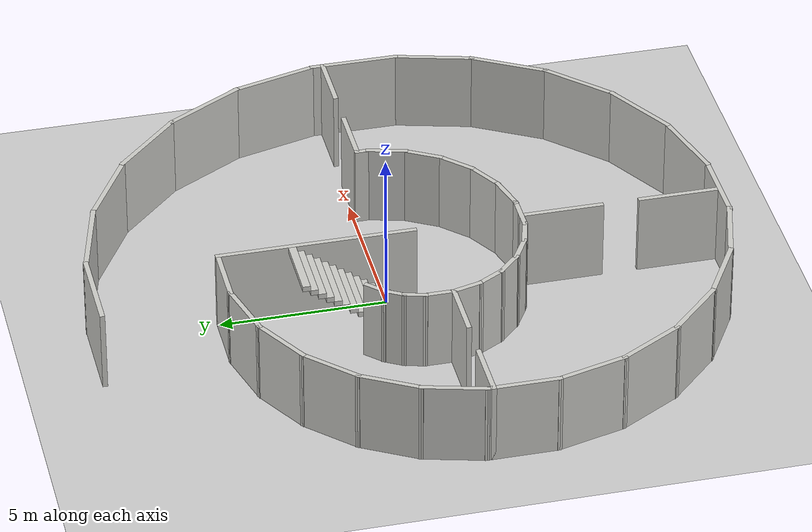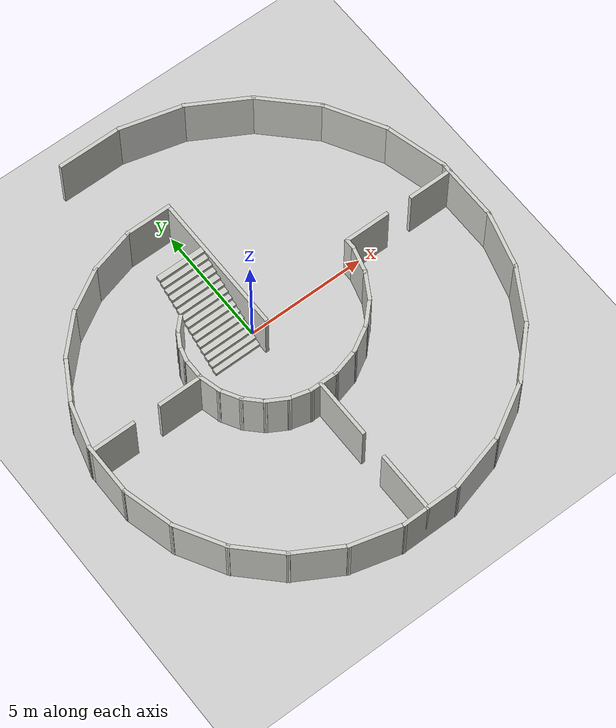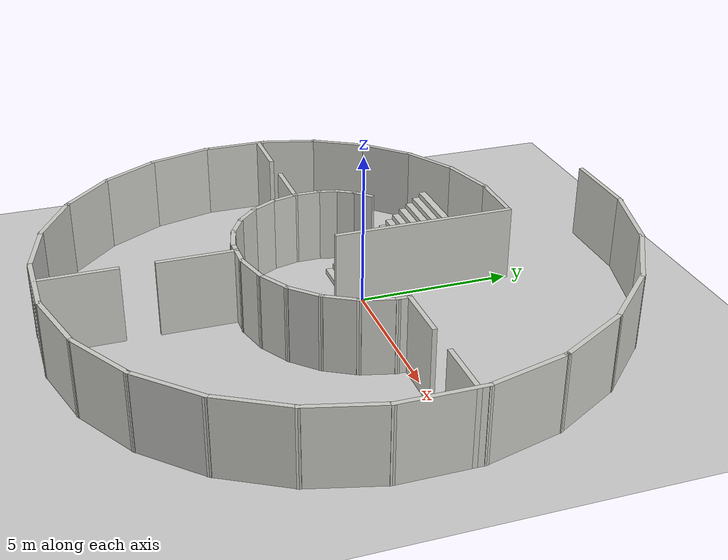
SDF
<sdf version="1.6">
 <world name="default">
  <model name="ground_plane">
   <static>1</static>
   <link name="link">
    <collision name="collision">
     <geometry><plane><normal>0 0 1</normal><size>100 100</size></plane></geometry>
     <surface>
      <contact><collide_bitmask>65535</collide_bitmask></contact>
      <friction><ode><mu>100</mu><mu2>50</mu2></ode></friction>
     </surface>
    </collision>
    <visual name="visual">
     <cast_shadows>0</cast_shadows>
     <geometry><plane><normal>0 0 1</normal><size>100 100</size></plane></geometry>
     <material>
      <script><uri>file://media/materials/scripts/gazebo.material</uri><name>Gazebo/Grey</name></script>
     </material>
    </visual>
   </link>
  </model>
  <gravity>0 0 -9.8</gravity>
  <magnetic_field>6e-06 2.3e-05 -4.2e-05</magnetic_field>
  <atmosphere type="adiabatic"/>
  <physics name="default_physics" default="0" type="ode">
   <max_step_size>0.001</max_step_size>
   <real_time_factor>1</real_time_factor>
   <real_time_update_rate>1000</real_time_update_rate>
  </physics>
  <scene><ambient>0.4 0.4 0.4 1</ambient><background>0.7 0.7 0.7 1</background><shadows>1</shadows></scene>
  <spherical_coordinates>
   <surface_model>EARTH_WGS84</surface_model>
   <latitude_deg>0</latitude_deg>
   <longitude_deg>0</longitude_deg>
   <elevation>0</elevation>
   <heading_deg>0</heading_deg>
  </spherical_coordinates>
  <light name="user_point_light_0" type="point">
   <pose>5.33979 1.74403 1 0 -0 0</pose>
   <diffuse>0.5 0.5 0.5 1</diffuse>
   <specular>0.1 0.1 0.1 1</specular>
   <attenuation>
    <range>20</range>
    <constant>0.5</constant>
    <linear>0.01</linear>
    <quadratic>0.001</quadratic>
   </attenuation>
   <cast_shadows>0</cast_shadows>
   <direction>0 0 -1</direction>
  </light>
  <light name="user_point_light_1" type="point">
   <pose>5.02482 -5.12639 1 0 -0 0</pose>
   <diffuse>0.5 0.5 0.5 1</diffuse>
   <specular>0.1 0.1 0.1 1</specular>
   <attenuation>
    <range>20</range>
    <constant>0.5</constant>
    <linear>0.01</linear>
    <quadratic>0.001</quadratic>
   </attenuation>
   <cast_shadows>0</cast_shadows>
   <direction>0 0 -1</direction>
  </light>
  <light name="user_point_light_2" type="point">
   <pose>-3.47131 -5.78016 1 0 -0 0</pose>
   <diffuse>0.5 0.5 0.5 1</diffuse>
   <specular>0.1 0.1 0.1 1</specular>
   <attenuation>
    <range>20</range>
    <constant>0.5</constant>
    <linear>0.01</linear>
    <quadratic>0.001</quadratic>
   </attenuation>
   <cast_shadows>0</cast_shadows>
   <direction>0 0 -1</direction>
  </light>
  <light name="user_point_light_3" type="point">
   <pose>-3.7593 2.5508 1 0 -0 0</pose>
   <diffuse>0.5 0.5 0.5 1</diffuse>
   <specular>0.1 0.1 0.1 1</specular>
   <attenuation>
    <range>20</range>
    <constant>0.5</constant>
    <linear>0.01</linear>
    <quadratic>0.001</quadratic>
   </attenuation>
   <cast_shadows>0</cast_shadows>
   <direction>0 0 -1</direction>
  </light>
  <model name="floor_plan">
   <link name="Stairs_0">
    <visual name="Stairs_0_Visual_8">
     <pose>-1.64058 2.08074 1.41667 0 -0 -3.14159</pose>
     <geometry><box><size>2 0.233333 0.166667</size></box></geometry>
     <material>
      <script><uri>file://media/materials/scripts/gazebo.material</uri><name>Gazebo/CeilingTiled</name></script>
      <ambient>1 1 1 1</ambient>
      <shader type="pixel"/>
     </material>
     <meta><layer>0</layer></meta>
    </visual>
    <visual name="Stairs_0_Visual_7">
     <pose>-1.64058 1.84741 1.25 0 -0 -3.14159</pose>
     <geometry><box><size>2 0.233333 0.166667</size></box></geometry>
     <material>
      <script><uri>file://media/materials/scripts/gazebo.material</uri><name>Gazebo/CeilingTiled</name></script>
      <ambient>1 1 1 1</ambient>
      <shader type="pixel"/>
     </material>
     <meta><layer>0</layer></meta>
    </visual>
    <visual name="Stairs_0_Visual_11">
     <pose>-1.64058 2.78074 1.91667 0 -0 -3.14159</pose>
     <geometry><box><size>2 0.233333 0.166667</size></box></geometry>
     <material>
      <script><uri>file://media/materials/scripts/gazebo.material</uri><name>Gazebo/CeilingTiled</name></script>
      <ambient>1 1 1 1</ambient>
      <shader type="pixel"/>
     </material>
     <meta><layer>0</layer></meta>
    </visual>
    <visual name="Stairs_0_Visual_0">
     <pose>-1.64058 0.214076 0.083333 0 -0 -3.14159</pose>
     <geometry><box><size>2 0.233333 0.166667</size></box></geometry>
     <material>
      <script><uri>file://media/materials/scripts/gazebo.material</uri><name>Gazebo/CeilingTiled</name></script>
      <ambient>1 1 1 1</ambient>
      <shader type="pixel"/>
     </material>
     <meta><layer>0</layer></meta>
    </visual>
    <visual name="Stairs_0_Visual_2">
     <pose>-1.64058 0.680742 0.416667 0 -0 -3.14159</pose>
     <geometry><box><size>2 0.233333 0.166667</size></box></geometry>
     <material>
      <script><uri>file://media/materials/scripts/gazebo.material</uri><name>Gazebo/CeilingTiled</name></script>
      <ambient>1 1 1 1</ambient>
      <shader type="pixel"/>
     </material>
     <meta><layer>0</layer></meta>
    </visual>
    <visual name="Stairs_0_Visual_3">
     <pose>-1.64058 0.914076 0.583333 0 -0 -3.14159</pose>
     <geometry><box><size>2 0.233333 0.166667</size></box></geometry>
     <material>
      <script><uri>file://media/materials/scripts/gazebo.material</uri><name>Gazebo/CeilingTiled</name></script>
      <ambient>1 1 1 1</ambient>
      <shader type="pixel"/>
     </material>
     <meta><layer>0</layer></meta>
    </visual>
    <visual name="Stairs_0_Visual_14">
     <pose>-1.64058 3.48074 2.41667 0 -0 -3.14159</pose>
     <geometry><box><size>2 0.233333 0.166667</size></box></geometry>
     <material>
      <script><uri>file://media/materials/scripts/gazebo.material</uri><name>Gazebo/CeilingTiled</name></script>
      <ambient>1 1 1 1</ambient>
      <shader type="pixel"/>
     </material>
     <meta><layer>0</layer></meta>
    </visual>
    <visual name="Stairs_0_Visual_1">
     <pose>-1.64058 0.447409 0.25 0 -0 -3.14159</pose>
     <geometry><box><size>2 0.233333 0.166667</size></box></geometry>
     <material>
      <script><uri>file://media/materials/scripts/gazebo.material</uri><name>Gazebo/CeilingTiled</name></script>
      <ambient>1 1 1 1</ambient>
      <shader type="pixel"/>
     </material>
     <meta><layer>0</layer></meta>
    </visual>
    <visual name="Stairs_0_Visual_6">
     <pose>-1.64058 1.61408 1.08333 0 -0 -3.14159</pose>
     <geometry><box><size>2 0.233333 0.166667</size></box></geometry>
     <material>
      <script><uri>file://media/materials/scripts/gazebo.material</uri><name>Gazebo/CeilingTiled</name></script>
      <ambient>1 1 1 1</ambient>
      <shader type="pixel"/>
     </material>
     <meta><layer>0</layer></meta>
    </visual>
    <visual name="Stairs_0_Visual_5">
     <pose>-1.64058 1.38074 0.916667 0 -0 -3.14159</pose>
     <geometry><box><size>2 0.233333 0.166667</size></box></geometry>
     <material>
      <script><uri>file://media/materials/scripts/gazebo.material</uri><name>Gazebo/CeilingTiled</name></script>
      <ambient>1 1 1 1</ambient>
      <shader type="pixel"/>
     </material>
     <meta><layer>0</layer></meta>
    </visual>
    <visual name="Stairs_0_Visual_12">
     <pose>-1.64058 3.01408 2.08333 0 -0 -3.14159</pose>
     <geometry><box><size>2 0.233333 0.166667</size></box></geometry>
     <material>
      <script><uri>file://media/materials/scripts/gazebo.material</uri><name>Gazebo/CeilingTiled</name></script>
      <ambient>1 1 1 1</ambient>
      <shader type="pixel"/>
     </material>
     <meta><layer>0</layer></meta>
    </visual>
    <visual name="Stairs_0_Visual_4">
     <pose>-1.64058 1.14741 0.75 0 -0 -3.14159</pose>
     <geometry><box><size>2 0.233333 0.166667</size></box></geometry>
     <material>
      <script><uri>file://media/materials/scripts/gazebo.material</uri><name>Gazebo/CeilingTiled</name></script>
      <ambient>1 1 1 1</ambient>
      <shader type="pixel"/>
     </material>
     <meta><layer>0</layer></meta>
    </visual>
    <visual name="Stairs_0_Visual_10">
     <pose>-1.64058 2.54741 1.75 0 -0 -3.14159</pose>
     <geometry><box><size>2 0.233333 0.166667</size></box></geometry>
     <material>
      <script><uri>file://media/materials/scripts/gazebo.material</uri><name>Gazebo/CeilingTiled</name></script>
      <ambient>1 1 1 1</ambient>
      <shader type="pixel"/>
     </material>
     <meta><layer>0</layer></meta>
    </visual>
    <visual name="Stairs_0_Visual_9">
     <pose>-1.64058 2.31408 1.58333 0 -0 -3.14159</pose>
     <geometry><box><size>2 0.233333 0.166667</size></box></geometry>
     <material>
      <script><uri>file://media/materials/scripts/gazebo.material</uri><name>Gazebo/CeilingTiled</name></script>
      <ambient>1 1 1 1</ambient>
      <shader type="pixel"/>
     </material>
     <meta><layer>0</layer></meta>
    </visual>
    <visual name="Stairs_0_Visual_13">
     <pose>-1.64058 3.24741 2.25 0 -0 -3.14159</pose>
     <geometry><box><size>2 0.233333 0.166667</size></box></geometry>
     <material>
      <script><uri>file://media/materials/scripts/gazebo.material</uri><name>Gazebo/CeilingTiled</name></script>
      <ambient>1 1 1 1</ambient>
      <shader type="pixel"/>
     </material>
     <meta><layer>0</layer></meta>
    </visual>
    <collision name="Stairs_0_Collision_0">
     <pose>-1.64058 0.214076 0.083333 0 0 -3.14159</pose>
     <geometry><box><size>2 0.233333 0.166667</size></box></geometry>
     <surface>
      <friction>
       <ode><mu>1</mu><mu2>1</mu2><fdir1>0 0 0</fdir1><slip1>0</slip1><slip2>0</slip2></ode>
       <torsional>
        <coefficient>1</coefficient>
        <patch_radius>0</patch_radius>
        <surface_radius>0</surface_radius>
        <use_patch_radius>1</use_patch_radius>
        <ode><slip>0</slip></ode>
       </torsional>
      </friction>
      <bounce><restitution_coefficient>0</restitution_coefficient><threshold>1e+06</threshold></bounce>
      <contact>
       <collide_without_contact>0</collide_without_contact>
       <collide_without_contact_bitmask>1</collide_without_contact_bitmask>
       <collide_bitmask>1</collide_bitmask>
       <ode>
        <soft_cfm>0</soft_cfm>
        <soft_erp>0.2</soft_erp>
        <kp>1e+13</kp>
        <kd>1</kd>
        <max_vel>0.01</max_vel>
        <min_depth>0</min_depth>
       </ode>
       <bullet>
        <split_impulse>1</split_impulse>
        <split_impulse_penetration_threshold>-0.01</split_impulse_penetration_threshold>
        <soft_cfm>0</soft_cfm>
        <soft_erp>0.2</soft_erp>
        <kp>1e+13</kp>
        <kd>1</kd>
       </bullet>
      </contact>
     </surface>
    </collision>
    <collision name="Stairs_0_Collision_12">
     <pose>-1.64058 3.01408 2.08333 0 0 -3.14159</pose>
     <geometry><box><size>2 0.233333 0.166667</size></box></geometry>
     <surface>
      <friction>
       <ode><mu>1</mu><mu2>1</mu2><fdir1>0 0 0</fdir1><slip1>0</slip1><slip2>0</slip2></ode>
       <torsional>
        <coefficient>1</coefficient>
        <patch_radius>0</patch_radius>
        <surface_radius>0</surface_radius>
        <use_patch_radius>1</use_patch_radius>
        <ode><slip>0</slip></ode>
       </torsional>
      </friction>
      <bounce><restitution_coefficient>0</restitution_coefficient><threshold>1e+06</threshold></bounce>
      <contact>
       <collide_without_contact>0</collide_without_contact>
       <collide_without_contact_bitmask>1</collide_without_contact_bitmask>
       <collide_bitmask>1</collide_bitmask>
       <ode>
        <soft_cfm>0</soft_cfm>
        <soft_erp>0.2</soft_erp>
        <kp>1e+13</kp>
        <kd>1</kd>
        <max_vel>0.01</max_vel>
        <min_depth>0</min_depth>
       </ode>
       <bullet>
        <split_impulse>1</split_impulse>
        <split_impulse_penetration_threshold>-0.01</split_impulse_penetration_threshold>
        <soft_cfm>0</soft_cfm>
        <soft_erp>0.2</soft_erp>
        <kp>1e+13</kp>
        <kd>1</kd>
       </bullet>
      </contact>
     </surface>
    </collision>
    <collision name="Stairs_0_Collision_4">
     <pose>-1.64058 1.14741 0.75 0 0 -3.14159</pose>
     <geometry><box><size>2 0.233333 0.166667</size></box></geometry>
     <surface>
      <friction>
       <ode><mu>1</mu><mu2>1</mu2><fdir1>0 0 0</fdir1><slip1>0</slip1><slip2>0</slip2></ode>
       <torsional>
        <coefficient>1</coefficient>
        <patch_radius>0</patch_radius>
        <surface_radius>0</surface_radius>
        <use_patch_radius>1</use_patch_radius>
        <ode><slip>0</slip></ode>
       </torsional>
      </friction>
      <bounce><restitution_coefficient>0</restitution_coefficient><threshold>1e+06</threshold></bounce>
      <contact>
       <collide_without_contact>0</collide_without_contact>
       <collide_without_contact_bitmask>1</collide_without_contact_bitmask>
       <collide_bitmask>1</collide_bitmask>
       <ode>
        <soft_cfm>0</soft_cfm>
        <soft_erp>0.2</soft_erp>
        <kp>1e+13</kp>
        <kd>1</kd>
        <max_vel>0.01</max_vel>
        <min_depth>0</min_depth>
       </ode>
       <bullet>
        <split_impulse>1</split_impulse>
        <split_impulse_penetration_threshold>-0.01</split_impulse_penetration_threshold>
        <soft_cfm>0</soft_cfm>
        <soft_erp>0.2</soft_erp>
        <kp>1e+13</kp>
        <kd>1</kd>
       </bullet>
      </contact>
     </surface>
    </collision>
    <collision name="Stairs_0_Collision_8">
     <pose>-1.64058 2.08074 1.41667 0 0 -3.14159</pose>
     <geometry><box><size>2 0.233333 0.166667</size></box></geometry>
     <surface>
      <friction>
       <ode><mu>1</mu><mu2>1</mu2><fdir1>0 0 0</fdir1><slip1>0</slip1><slip2>0</slip2></ode>
       <torsional>
        <coefficient>1</coefficient>
        <patch_radius>0</patch_radius>
        <surface_radius>0</surface_radius>
        <use_patch_radius>1</use_patch_radius>
        <ode><slip>0</slip></ode>
       </torsional>
      </friction>
      <bounce><restitution_coefficient>0</restitution_coefficient><threshold>1e+06</threshold></bounce>
      <contact>
       <collide_without_contact>0</collide_without_contact>
       <collide_without_contact_bitmask>1</collide_without_contact_bitmask>
       <collide_bitmask>1</collide_bitmask>
       <ode>
        <soft_cfm>0</soft_cfm>
        <soft_erp>0.2</soft_erp>
        <kp>1e+13</kp>
        <kd>1</kd>
        <max_vel>0.01</max_vel>
        <min_depth>0</min_depth>
       </ode>
       <bullet>
        <split_impulse>1</split_impulse>
        <split_impulse_penetration_threshold>-0.01</split_impulse_penetration_threshold>
        <soft_cfm>0</soft_cfm>
        <soft_erp>0.2</soft_erp>
        <kp>1e+13</kp>
        <kd>1</kd>
       </bullet>
      </contact>
     </surface>
    </collision>
    <collision name="Stairs_0_Collision_11">
     <pose>-1.64058 2.78074 1.91667 0 0 -3.14159</pose>
     <geometry><box><size>2 0.233333 0.166667</size></box></geometry>
     <surface>
      <friction>
       <ode><mu>1</mu><mu2>1</mu2><fdir1>0 0 0</fdir1><slip1>0</slip1><slip2>0</slip2></ode>
       <torsional>
        <coefficient>1</coefficient>
        <patch_radius>0</patch_radius>
        <surface_radius>0</surface_radius>
        <use_patch_radius>1</use_patch_radius>
        <ode><slip>0</slip></ode>
       </torsional>
      </friction>
      <bounce><restitution_coefficient>0</restitution_coefficient><threshold>1e+06</threshold></bounce>
      <contact>
       <collide_without_contact>0</collide_without_contact>
       <collide_without_contact_bitmask>1</collide_without_contact_bitmask>
       <collide_bitmask>1</collide_bitmask>
       <ode>
        <soft_cfm>0</soft_cfm>
        <soft_erp>0.2</soft_erp>
        <kp>1e+13</kp>
        <kd>1</kd>
        <max_vel>0.01</max_vel>
        <min_depth>0</min_depth>
       </ode>
       <bullet>
        <split_impulse>1</split_impulse>
        <split_impulse_penetration_threshold>-0.01</split_impulse_penetration_threshold>
        <soft_cfm>0</soft_cfm>
        <soft_erp>0.2</soft_erp>
        <kp>1e+13</kp>
        <kd>1</kd>
       </bullet>
      </contact>
     </surface>
    </collision>
    <collision name="Stairs_0_Collision_6">
     <pose>-1.64058 1.61408 1.08333 0 0 -3.14159</pose>
     <geometry><box><size>2 0.233333 0.166667</size></box></geometry>
     <surface>
      <friction>
       <ode><mu>1</mu><mu2>1</mu2><fdir1>0 0 0</fdir1><slip1>0</slip1><slip2>0</slip2></ode>
       <torsional>
        <coefficient>1</coefficient>
        <patch_radius>0</patch_radius>
        <surface_radius>0</surface_radius>
        <use_patch_radius>1</use_patch_radius>
        <ode><slip>0</slip></ode>
       </torsional>
      </friction>
      <bounce><restitution_coefficient>0</restitution_coefficient><threshold>1e+06</threshold></bounce>
      <contact>
       <collide_without_contact>0</collide_without_contact>
       <collide_without_contact_bitmask>1</collide_without_contact_bitmask>
       <collide_bitmask>1</collide_bitmask>
       <ode>
        <soft_cfm>0</soft_cfm>
        <soft_erp>0.2</soft_erp>
        <kp>1e+13</kp>
        <kd>1</kd>
        <max_vel>0.01</max_vel>
        <min_depth>0</min_depth>
       </ode>
       <bullet>
        <split_impulse>1</split_impulse>
        <split_impulse_penetration_threshold>-0.01</split_impulse_penetration_threshold>
        <soft_cfm>0</soft_cfm>
        <soft_erp>0.2</soft_erp>
        <kp>1e+13</kp>
        <kd>1</kd>
       </bullet>
      </contact>
     </surface>
    </collision>
    <collision name="Stairs_0_Collision_1">
     <pose>-1.64058 0.447409 0.25 0 0 -3.14159</pose>
     <geometry><box><size>2 0.233333 0.166667</size></box></geometry>
     <surface>
      <friction>
       <ode><mu>1</mu><mu2>1</mu2><fdir1>0 0 0</fdir1><slip1>0</slip1><slip2>0</slip2></ode>
       <torsional>
        <coefficient>1</coefficient>
        <patch_radius>0</patch_radius>
        <surface_radius>0</surface_radius>
        <use_patch_radius>1</use_patch_radius>
        <ode><slip>0</slip></ode>
       </torsional>
      </friction>
      <bounce><restitution_coefficient>0</restitution_coefficient><threshold>1e+06</threshold></bounce>
      <contact>
       <collide_without_contact>0</collide_without_contact>
       <collide_without_contact_bitmask>1</collide_without_contact_bitmask>
       <collide_bitmask>1</collide_bitmask>
       <ode>
        <soft_cfm>0</soft_cfm>
        <soft_erp>0.2</soft_erp>
        <kp>1e+13</kp>
        <kd>1</kd>
        <max_vel>0.01</max_vel>
        <min_depth>0</min_depth>
       </ode>
       <bullet>
        <split_impulse>1</split_impulse>
        <split_impulse_penetration_threshold>-0.01</split_impulse_penetration_threshold>
        <soft_cfm>0</soft_cfm>
        <soft_erp>0.2</soft_erp>
        <kp>1e+13</kp>
        <kd>1</kd>
       </bullet>
      </contact>
     </surface>
    </collision>
    <collision name="Stairs_0_Collision_7">
     <pose>-1.64058 1.84741 1.25 0 0 -3.14159</pose>
     <geometry><box><size>2 0.233333 0.166667</size></box></geometry>
     <surface>
      <friction>
       <ode><mu>1</mu><mu2>1</mu2><fdir1>0 0 0</fdir1><slip1>0</slip1><slip2>0</slip2></ode>
       <torsional>
        <coefficient>1</coefficient>
        <patch_radius>0</patch_radius>
        <surface_radius>0</surface_radius>
        <use_patch_radius>1</use_patch_radius>
        <ode><slip>0</slip></ode>
       </torsional>
      </friction>
      <bounce><restitution_coefficient>0</restitution_coefficient><threshold>1e+06</threshold></bounce>
      <contact>
       <collide_without_contact>0</collide_without_contact>
       <collide_without_contact_bitmask>1</collide_without_contact_bitmask>
       <collide_bitmask>1</collide_bitmask>
       <ode>
        <soft_cfm>0</soft_cfm>
        <soft_erp>0.2</soft_erp>
        <kp>1e+13</kp>
        <kd>1</kd>
        <max_vel>0.01</max_vel>
        <min_depth>0</min_depth>
       </ode>
       <bullet>
        <split_impulse>1</split_impulse>
        <split_impulse_penetration_threshold>-0.01</split_impulse_penetration_threshold>
        <soft_cfm>0</soft_cfm>
        <soft_erp>0.2</soft_erp>
        <kp>1e+13</kp>
        <kd>1</kd>
       </bullet>
      </contact>
     </surface>
    </collision>
    <collision name="Stairs_0_Collision_5">
     <pose>-1.64058 1.38074 0.916667 0 0 -3.14159</pose>
     <geometry><box><size>2 0.233333 0.166667</size></box></geometry>
     <surface>
      <friction>
       <ode><mu>1</mu><mu2>1</mu2><fdir1>0 0 0</fdir1><slip1>0</slip1><slip2>0</slip2></ode>
       <torsional>
        <coefficient>1</coefficient>
        <patch_radius>0</patch_radius>
        <surface_radius>0</surface_radius>
        <use_patch_radius>1</use_patch_radius>
        <ode><slip>0</slip></ode>
       </torsional>
      </friction>
      <bounce><restitution_coefficient>0</restitution_coefficient><threshold>1e+06</threshold></bounce>
      <contact>
       <collide_without_contact>0</collide_without_contact>
       <collide_without_contact_bitmask>1</collide_without_contact_bitmask>
       <collide_bitmask>1</collide_bitmask>
       <ode>
        <soft_cfm>0</soft_cfm>
        <soft_erp>0.2</soft_erp>
        <kp>1e+13</kp>
        <kd>1</kd>
        <max_vel>0.01</max_vel>
        <min_depth>0</min_depth>
       </ode>
       <bullet>
        <split_impulse>1</split_impulse>
        <split_impulse_penetration_threshold>-0.01</split_impulse_penetration_threshold>
        <soft_cfm>0</soft_cfm>
        <soft_erp>0.2</soft_erp>
        <kp>1e+13</kp>
        <kd>1</kd>
       </bullet>
      </contact>
     </surface>
    </collision>
    <collision name="Stairs_0_Collision_10">
     <pose>-1.64058 2.54741 1.75 0 0 -3.14159</pose>
     <geometry><box><size>2 0.233333 0.166667</size></box></geometry>
     <surface>
      <friction>
       <ode><mu>1</mu><mu2>1</mu2><fdir1>0 0 0</fdir1><slip1>0</slip1><slip2>0</slip2></ode>
       <torsional>
        <coefficient>1</coefficient>
        <patch_radius>0</patch_radius>
        <surface_radius>0</surface_radius>
        <use_patch_radius>1</use_patch_radius>
        <ode><slip>0</slip></ode>
       </torsional>
      </friction>
      <bounce><restitution_coefficient>0</restitution_coefficient><threshold>1e+06</threshold></bounce>
      <contact>
       <collide_without_contact>0</collide_without_contact>
       <collide_without_contact_bitmask>1</collide_without_contact_bitmask>
       <collide_bitmask>1</collide_bitmask>
       <ode>
        <soft_cfm>0</soft_cfm>
        <soft_erp>0.2</soft_erp>
        <kp>1e+13</kp>
        <kd>1</kd>
        <max_vel>0.01</max_vel>
        <min_depth>0</min_depth>
       </ode>
       <bullet>
        <split_impulse>1</split_impulse>
        <split_impulse_penetration_threshold>-0.01</split_impulse_penetration_threshold>
        <soft_cfm>0</soft_cfm>
        <soft_erp>0.2</soft_erp>
        <kp>1e+13</kp>
        <kd>1</kd>
       </bullet>
      </contact>
     </surface>
    </collision>
    <collision name="Stairs_0_Collision_9">
     <pose>-1.64058 2.31408 1.58333 0 0 -3.14159</pose>
     <geometry><box><size>2 0.233333 0.166667</size></box></geometry>
     <surface>
      <friction>
       <ode><mu>1</mu><mu2>1</mu2><fdir1>0 0 0</fdir1><slip1>0</slip1><slip2>0</slip2></ode>
       <torsional>
        <coefficient>1</coefficient>
        <patch_radius>0</patch_radius>
        <surface_radius>0</surface_radius>
        <use_patch_radius>1</use_patch_radius>
        <ode><slip>0</slip></ode>
       </torsional>
      </friction>
      <bounce><restitution_coefficient>0</restitution_coefficient><threshold>1e+06</threshold></bounce>
      <contact>
       <collide_without_contact>0</collide_without_contact>
       <collide_without_contact_bitmask>1</collide_without_contact_bitmask>
       <collide_bitmask>1</collide_bitmask>
       <ode>
        <soft_cfm>0</soft_cfm>
        <soft_erp>0.2</soft_erp>
        <kp>1e+13</kp>
        <kd>1</kd>
        <max_vel>0.01</max_vel>
        <min_depth>0</min_depth>
       </ode>
       <bullet>
        <split_impulse>1</split_impulse>
        <split_impulse_penetration_threshold>-0.01</split_impulse_penetration_threshold>
        <soft_cfm>0</soft_cfm>
        <soft_erp>0.2</soft_erp>
        <kp>1e+13</kp>
        <kd>1</kd>
       </bullet>
      </contact>
     </surface>
    </collision>
    <collision name="Stairs_0_Collision_3">
     <pose>-1.64058 0.914076 0.583333 0 0 -3.14159</pose>
     <geometry><box><size>2 0.233333 0.166667</size></box></geometry>
     <surface>
      <friction>
       <ode><mu>1</mu><mu2>1</mu2><fdir1>0 0 0</fdir1><slip1>0</slip1><slip2>0</slip2></ode>
       <torsional>
        <coefficient>1</coefficient>
        <patch_radius>0</patch_radius>
        <surface_radius>0</surface_radius>
        <use_patch_radius>1</use_patch_radius>
        <ode><slip>0</slip></ode>
       </torsional>
      </friction>
      <bounce><restitution_coefficient>0</restitution_coefficient><threshold>1e+06</threshold></bounce>
      <contact>
       <collide_without_contact>0</collide_without_contact>
       <collide_without_contact_bitmask>1</collide_without_contact_bitmask>
       <collide_bitmask>1</collide_bitmask>
       <ode>
        <soft_cfm>0</soft_cfm>
        <soft_erp>0.2</soft_erp>
        <kp>1e+13</kp>
        <kd>1</kd>
        <max_vel>0.01</max_vel>
        <min_depth>0</min_depth>
       </ode>
       <bullet>
        <split_impulse>1</split_impulse>
        <split_impulse_penetration_threshold>-0.01</split_impulse_penetration_threshold>
        <soft_cfm>0</soft_cfm>
        <soft_erp>0.2</soft_erp>
        <kp>1e+13</kp>
        <kd>1</kd>
       </bullet>
      </contact>
     </surface>
    </collision>
    <collision name="Stairs_0_Collision_2">
     <pose>-1.64058 0.680742 0.416667 0 0 -3.14159</pose>
     <geometry><box><size>2 0.233333 0.166667</size></box></geometry>
     <surface>
      <friction>
       <ode><mu>1</mu><mu2>1</mu2><fdir1>0 0 0</fdir1><slip1>0</slip1><slip2>0</slip2></ode>
       <torsional>
        <coefficient>1</coefficient>
        <patch_radius>0</patch_radius>
        <surface_radius>0</surface_radius>
        <use_patch_radius>1</use_patch_radius>
        <ode><slip>0</slip></ode>
       </torsional>
      </friction>
      <bounce><restitution_coefficient>0</restitution_coefficient><threshold>1e+06</threshold></bounce>
      <contact>
       <collide_without_contact>0</collide_without_contact>
       <collide_without_contact_bitmask>1</collide_without_contact_bitmask>
       <collide_bitmask>1</collide_bitmask>
       <ode>
        <soft_cfm>0</soft_cfm>
        <soft_erp>0.2</soft_erp>
        <kp>1e+13</kp>
        <kd>1</kd>
        <max_vel>0.01</max_vel>
        <min_depth>0</min_depth>
       </ode>
       <bullet>
        <split_impulse>1</split_impulse>
        <split_impulse_penetration_threshold>-0.01</split_impulse_penetration_threshold>
        <soft_cfm>0</soft_cfm>
        <soft_erp>0.2</soft_erp>
        <kp>1e+13</kp>
        <kd>1</kd>
       </bullet>
      </contact>
     </surface>
    </collision>
    <collision name="Stairs_0_Collision_13">
     <pose>-1.64058 3.24741 2.25 0 0 -3.14159</pose>
     <geometry><box><size>2 0.233333 0.166667</size></box></geometry>
     <surface>
      <friction>
       <ode><mu>1</mu><mu2>1</mu2><fdir1>0 0 0</fdir1><slip1>0</slip1><slip2>0</slip2></ode>
       <torsional>
        <coefficient>1</coefficient>
        <patch_radius>0</patch_radius>
        <surface_radius>0</surface_radius>
        <use_patch_radius>1</use_patch_radius>
        <ode><slip>0</slip></ode>
       </torsional>
      </friction>
      <bounce><restitution_coefficient>0</restitution_coefficient><threshold>1e+06</threshold></bounce>
      <contact>
       <collide_without_contact>0</collide_without_contact>
       <collide_without_contact_bitmask>1</collide_without_contact_bitmask>
       <collide_bitmask>1</collide_bitmask>
       <ode>
        <soft_cfm>0</soft_cfm>
        <soft_erp>0.2</soft_erp>
        <kp>1e+13</kp>
        <kd>1</kd>
        <max_vel>0.01</max_vel>
        <min_depth>0</min_depth>
       </ode>
       <bullet>
        <split_impulse>1</split_impulse>
        <split_impulse_penetration_threshold>-0.01</split_impulse_penetration_threshold>
        <soft_cfm>0</soft_cfm>
        <soft_erp>0.2</soft_erp>
        <kp>1e+13</kp>
        <kd>1</kd>
       </bullet>
      </contact>
     </surface>
    </collision>
    <collision name="Stairs_0_Collision_14">
     <pose>-1.64058 3.48074 2.41667 0 0 -3.14159</pose>
     <geometry><box><size>2 0.233333 0.166667</size></box></geometry>
     <surface>
      <friction>
       <ode><mu>1</mu><mu2>1</mu2><fdir1>0 0 0</fdir1><slip1>0</slip1><slip2>0</slip2></ode>
       <torsional>
        <coefficient>1</coefficient>
        <patch_radius>0</patch_radius>
        <surface_radius>0</surface_radius>
        <use_patch_radius>1</use_patch_radius>
        <ode><slip>0</slip></ode>
       </torsional>
      </friction>
      <bounce><restitution_coefficient>0</restitution_coefficient><threshold>1e+06</threshold></bounce>
      <contact>
       <collide_without_contact>0</collide_without_contact>
       <collide_without_contact_bitmask>1</collide_without_contact_bitmask>
       <collide_bitmask>1</collide_bitmask>
       <ode>
        <soft_cfm>0</soft_cfm>
        <soft_erp>0.2</soft_erp>
        <kp>1e+13</kp>
        <kd>1</kd>
        <max_vel>0.01</max_vel>
        <min_depth>0</min_depth>
       </ode>
       <bullet>
        <split_impulse>1</split_impulse>
        <split_impulse_penetration_threshold>-0.01</split_impulse_penetration_threshold>
        <soft_cfm>0</soft_cfm>
        <soft_erp>0.2</soft_erp>
        <kp>1e+13</kp>
        <kd>1</kd>
       </bullet>
      </contact>
     </surface>
    </collision>
   </link>
   <link name="Wall_10">
    <pose>-8.27721 0.464854 0 0 0 -1.83257</pose>
    <visual name="Wall_10_Visual">
     <pose>0 0 1.25 0 -0 0</pose>
     <geometry><box><size>2 0.15 2.5</size></box></geometry>
     <material>
      <script><uri>file://media/materials/scripts/gazebo.material</uri><name>Gazebo/CeilingTiled</name></script>
      <ambient>1 1 1 1</ambient>
      <shader type="pixel"/>
     </material>
     <meta><layer>0</layer></meta>
    </visual>
    <collision name="Wall_10_Collision">
     <pose>0 0 1.25 0 -0 0</pose>
     <geometry><box><size>2 0.15 2.5</size></box></geometry>
     <surface>
      <friction>
       <ode><mu>1</mu><mu2>1</mu2><fdir1>0 0 0</fdir1><slip1>0</slip1><slip2>0</slip2></ode>
       <torsional>
        <coefficient>1</coefficient>
        <patch_radius>0</patch_radius>
        <surface_radius>0</surface_radius>
        <use_patch_radius>1</use_patch_radius>
        <ode><slip>0</slip></ode>
       </torsional>
      </friction>
      <bounce><restitution_coefficient>0</restitution_coefficient><threshold>1e+06</threshold></bounce>
      <contact>
       <collide_without_contact>0</collide_without_contact>
       <collide_without_contact_bitmask>1</collide_without_contact_bitmask>
       <collide_bitmask>1</collide_bitmask>
       <ode>
        <soft_cfm>0</soft_cfm>
        <soft_erp>0.2</soft_erp>
        <kp>1e+13</kp>
        <kd>1</kd>
        <max_vel>0.01</max_vel>
        <min_depth>0</min_depth>
       </ode>
       <bullet>
        <split_impulse>1</split_impulse>
        <split_impulse_penetration_threshold>-0.01</split_impulse_penetration_threshold>
        <soft_cfm>0</soft_cfm>
        <soft_erp>0.2</soft_erp>
        <kp>1e+13</kp>
        <kd>1</kd>
       </bullet>
      </contact>
     </surface>
    </collision>
   </link>
   <link name="Wall_12">
    <pose>-8.51658 -1.47859 0 0 0 -1.5708</pose>
    <visual name="Wall_12_Visual">
     <pose>0 0 1.25 0 -0 0</pose>
     <geometry><box><size>2.25 0.15 2.5</size></box></geometry>
     <material>
      <script><uri>file://media/materials/scripts/gazebo.material</uri><name>Gazebo/CeilingTiled</name></script>
      <ambient>1 1 1 1</ambient>
      <shader type="pixel"/>
     </material>
     <meta><layer>0</layer></meta>
    </visual>
    <collision name="Wall_12_Collision">
     <pose>0 0 1.25 0 -0 0</pose>
     <geometry><box><size>2.25 0.15 2.5</size></box></geometry>
     <surface>
      <friction>
       <ode><mu>1</mu><mu2>1</mu2><fdir1>0 0 0</fdir1><slip1>0</slip1><slip2>0</slip2></ode>
       <torsional>
        <coefficient>1</coefficient>
        <patch_radius>0</patch_radius>
        <surface_radius>0</surface_radius>
        <use_patch_radius>1</use_patch_radius>
        <ode><slip>0</slip></ode>
       </torsional>
      </friction>
      <bounce><restitution_coefficient>0</restitution_coefficient><threshold>1e+06</threshold></bounce>
      <contact>
       <collide_without_contact>0</collide_without_contact>
       <collide_without_contact_bitmask>1</collide_without_contact_bitmask>
       <collide_bitmask>1</collide_bitmask>
       <ode>
        <soft_cfm>0</soft_cfm>
        <soft_erp>0.2</soft_erp>
        <kp>1e+13</kp>
        <kd>1</kd>
        <max_vel>0.01</max_vel>
        <min_depth>0</min_depth>
       </ode>
       <bullet>
        <split_impulse>1</split_impulse>
        <split_impulse_penetration_threshold>-0.01</split_impulse_penetration_threshold>
        <soft_cfm>0</soft_cfm>
        <soft_erp>0.2</soft_erp>
        <kp>1e+13</kp>
        <kd>1</kd>
       </bullet>
      </contact>
     </surface>
    </collision>
   </link>
   <link name="Wall_15">
    <pose>-8.24485 -3.54285 0 0 0 -1.30904</pose>
    <visual name="Wall_15_Visual">
     <pose>0 0 1.25 0 -0 0</pose>
     <geometry><box><size>2.25 0.15 2.5</size></box></geometry>
     <material>
      <script><uri>file://media/materials/scripts/gazebo.material</uri><name>Gazebo/CeilingTiled</name></script>
      <ambient>1 1 1 1</ambient>
      <shader type="pixel"/>
     </material>
     <meta><layer>0</layer></meta>
    </visual>
    <collision name="Wall_15_Collision">
     <pose>0 0 1.25 0 -0 0</pose>
     <geometry><box><size>2.25 0.15 2.5</size></box></geometry>
     <surface>
      <friction>
       <ode><mu>1</mu><mu2>1</mu2><fdir1>0 0 0</fdir1><slip1>0</slip1><slip2>0</slip2></ode>
       <torsional>
        <coefficient>1</coefficient>
        <patch_radius>0</patch_radius>
        <surface_radius>0</surface_radius>
        <use_patch_radius>1</use_patch_radius>
        <ode><slip>0</slip></ode>
       </torsional>
      </friction>
      <bounce><restitution_coefficient>0</restitution_coefficient><threshold>1e+06</threshold></bounce>
      <contact>
       <collide_without_contact>0</collide_without_contact>
       <collide_without_contact_bitmask>1</collide_without_contact_bitmask>
       <collide_bitmask>1</collide_bitmask>
       <ode>
        <soft_cfm>0</soft_cfm>
        <soft_erp>0.2</soft_erp>
        <kp>1e+13</kp>
        <kd>1</kd>
        <max_vel>0.01</max_vel>
        <min_depth>0</min_depth>
       </ode>
       <bullet>
        <split_impulse>1</split_impulse>
        <split_impulse_penetration_threshold>-0.01</split_impulse_penetration_threshold>
        <soft_cfm>0</soft_cfm>
        <soft_erp>0.2</soft_erp>
        <kp>1e+13</kp>
        <kd>1</kd>
       </bullet>
      </contact>
     </surface>
    </collision>
   </link>
   <link name="Wall_16">
    <pose>-7.44813 -5.46643 0 0 0 -1.0472</pose>
    <visual name="Wall_16_Visual">
     <pose>0 0 1.25 0 -0 0</pose>
     <geometry><box><size>2.25 0.15 2.5</size></box></geometry>
     <material>
      <script><uri>file://media/materials/scripts/gazebo.material</uri><name>Gazebo/CeilingTiled</name></script>
      <ambient>1 1 1 1</ambient>
      <shader type="pixel"/>
     </material>
     <meta><layer>0</layer></meta>
    </visual>
    <collision name="Wall_16_Collision">
     <pose>0 0 1.25 0 -0 0</pose>
     <geometry><box><size>2.25 0.15 2.5</size></box></geometry>
     <surface>
      <friction>
       <ode><mu>1</mu><mu2>1</mu2><fdir1>0 0 0</fdir1><slip1>0</slip1><slip2>0</slip2></ode>
       <torsional>
        <coefficient>1</coefficient>
        <patch_radius>0</patch_radius>
        <surface_radius>0</surface_radius>
        <use_patch_radius>1</use_patch_radius>
        <ode><slip>0</slip></ode>
       </torsional>
      </friction>
      <bounce><restitution_coefficient>0</restitution_coefficient><threshold>1e+06</threshold></bounce>
      <contact>
       <collide_without_contact>0</collide_without_contact>
       <collide_without_contact_bitmask>1</collide_without_contact_bitmask>
       <collide_bitmask>1</collide_bitmask>
       <ode>
        <soft_cfm>0</soft_cfm>
        <soft_erp>0.2</soft_erp>
        <kp>1e+13</kp>
        <kd>1</kd>
        <max_vel>0.01</max_vel>
        <min_depth>0</min_depth>
       </ode>
       <bullet>
        <split_impulse>1</split_impulse>
        <split_impulse_penetration_threshold>-0.01</split_impulse_penetration_threshold>
        <soft_cfm>0</soft_cfm>
        <soft_erp>0.2</soft_erp>
        <kp>1e+13</kp>
        <kd>1</kd>
       </bullet>
      </contact>
     </surface>
    </collision>
   </link>
   <link name="Wall_18">
    <pose>-6.18067 -7.11822 0 0 0 -0.785398</pose>
    <visual name="Wall_18_Visual">
     <pose>0 0 1.25 0 -0 0</pose>
     <geometry><box><size>2.25 0.15 2.5</size></box></geometry>
     <material>
      <script><uri>file://media/materials/scripts/gazebo.material</uri><name>Gazebo/CeilingTiled</name></script>
      <ambient>1 1 1 1</ambient>
      <shader type="pixel"/>
     </material>
     <meta><layer>0</layer></meta>
    </visual>
    <collision name="Wall_18_Collision">
     <pose>0 0 1.25 0 -0 0</pose>
     <geometry><box><size>2.25 0.15 2.5</size></box></geometry>
     <surface>
      <friction>
       <ode><mu>1</mu><mu2>1</mu2><fdir1>0 0 0</fdir1><slip1>0</slip1><slip2>0</slip2></ode>
       <torsional>
        <coefficient>1</coefficient>
        <patch_radius>0</patch_radius>
        <surface_radius>0</surface_radius>
        <use_patch_radius>1</use_patch_radius>
        <ode><slip>0</slip></ode>
       </torsional>
      </friction>
      <bounce><restitution_coefficient>0</restitution_coefficient><threshold>1e+06</threshold></bounce>
      <contact>
       <collide_without_contact>0</collide_without_contact>
       <collide_without_contact_bitmask>1</collide_without_contact_bitmask>
       <collide_bitmask>1</collide_bitmask>
       <ode>
        <soft_cfm>0</soft_cfm>
        <soft_erp>0.2</soft_erp>
        <kp>1e+13</kp>
        <kd>1</kd>
        <max_vel>0.01</max_vel>
        <min_depth>0</min_depth>
       </ode>
       <bullet>
        <split_impulse>1</split_impulse>
        <split_impulse_penetration_threshold>-0.01</split_impulse_penetration_threshold>
        <soft_cfm>0</soft_cfm>
        <soft_erp>0.2</soft_erp>
        <kp>1e+13</kp>
        <kd>1</kd>
       </bullet>
      </contact>
     </surface>
    </collision>
   </link>
   <link name="Wall_2">
    <pose>-1.49058 5.67241 0 0 -0 0</pose>
    <visual name="Wall_2_Visual">
     <pose>0 0 1.25 0 -0 0</pose>
     <geometry><box><size>2 0.15 2.5</size></box></geometry>
     <material>
      <script><uri>file://media/materials/scripts/gazebo.material</uri><name>Gazebo/CeilingTiled</name></script>
      <ambient>1 1 1 1</ambient>
      <shader type="pixel"/>
     </material>
     <meta><layer>0</layer></meta>
    </visual>
    <collision name="Wall_2_Collision">
     <pose>0 0 1.25 0 -0 0</pose>
     <geometry><box><size>2 0.15 2.5</size></box></geometry>
     <surface>
      <friction>
       <ode><mu>1</mu><mu2>1</mu2><fdir1>0 0 0</fdir1><slip1>0</slip1><slip2>0</slip2></ode>
       <torsional>
        <coefficient>1</coefficient>
        <patch_radius>0</patch_radius>
        <surface_radius>0</surface_radius>
        <use_patch_radius>1</use_patch_radius>
        <ode><slip>0</slip></ode>
       </torsional>
      </friction>
      <bounce><restitution_coefficient>0</restitution_coefficient><threshold>1e+06</threshold></bounce>
      <contact>
       <collide_without_contact>0</collide_without_contact>
       <collide_without_contact_bitmask>1</collide_without_contact_bitmask>
       <collide_bitmask>1</collide_bitmask>
       <ode>
        <soft_cfm>0</soft_cfm>
        <soft_erp>0.2</soft_erp>
        <kp>1e+13</kp>
        <kd>1</kd>
        <max_vel>0.01</max_vel>
        <min_depth>0</min_depth>
       </ode>
       <bullet>
        <split_impulse>1</split_impulse>
        <split_impulse_penetration_threshold>-0.01</split_impulse_penetration_threshold>
        <soft_cfm>0</soft_cfm>
        <soft_erp>0.2</soft_erp>
        <kp>1e+13</kp>
        <kd>1</kd>
       </bullet>
      </contact>
     </surface>
    </collision>
   </link>
   <link name="Wall_20">
    <pose>-4.52888 -8.38569 0 0 0 -0.523599</pose>
    <visual name="Wall_20_Visual">
     <pose>0 0 1.25 0 -0 0</pose>
     <geometry><box><size>2.25 0.15 2.5</size></box></geometry>
     <material>
      <script><uri>file://media/materials/scripts/gazebo.material</uri><name>Gazebo/CeilingTiled</name></script>
      <ambient>1 1 1 1</ambient>
      <shader type="pixel"/>
     </material>
     <meta><layer>0</layer></meta>
    </visual>
    <collision name="Wall_20_Collision">
     <pose>0 0 1.25 0 -0 0</pose>
     <geometry><box><size>2.25 0.15 2.5</size></box></geometry>
     <surface>
      <friction>
       <ode><mu>1</mu><mu2>1</mu2><fdir1>0 0 0</fdir1><slip1>0</slip1><slip2>0</slip2></ode>
       <torsional>
        <coefficient>1</coefficient>
        <patch_radius>0</patch_radius>
        <surface_radius>0</surface_radius>
        <use_patch_radius>1</use_patch_radius>
        <ode><slip>0</slip></ode>
       </torsional>
      </friction>
      <bounce><restitution_coefficient>0</restitution_coefficient><threshold>1e+06</threshold></bounce>
      <contact>
       <collide_without_contact>0</collide_without_contact>
       <collide_without_contact_bitmask>1</collide_without_contact_bitmask>
       <collide_bitmask>1</collide_bitmask>
       <ode>
        <soft_cfm>0</soft_cfm>
        <soft_erp>0.2</soft_erp>
        <kp>1e+13</kp>
        <kd>1</kd>
        <max_vel>0.01</max_vel>
        <min_depth>0</min_depth>
       </ode>
       <bullet>
        <split_impulse>1</split_impulse>
        <split_impulse_penetration_threshold>-0.01</split_impulse_penetration_threshold>
        <soft_cfm>0</soft_cfm>
        <soft_erp>0.2</soft_erp>
        <kp>1e+13</kp>
        <kd>1</kd>
       </bullet>
      </contact>
     </surface>
    </collision>
   </link>
   <link name="Wall_21">
    <pose>-2.60557 -9.18264 0 0 0 -0.262035</pose>
    <visual name="Wall_21_Visual">
     <pose>0 0 1.25 0 -0 0</pose>
     <geometry><box><size>2.25 0.15 2.5</size></box></geometry>
     <material>
      <script><uri>file://media/materials/scripts/gazebo.material</uri><name>Gazebo/CeilingTiled</name></script>
      <ambient>1 1 1 1</ambient>
      <shader type="pixel"/>
     </material>
     <meta><layer>0</layer></meta>
    </visual>
    <collision name="Wall_21_Collision">
     <pose>0 0 1.25 0 -0 0</pose>
     <geometry><box><size>2.25 0.15 2.5</size></box></geometry>
     <surface>
      <friction>
       <ode><mu>1</mu><mu2>1</mu2><fdir1>0 0 0</fdir1><slip1>0</slip1><slip2>0</slip2></ode>
       <torsional>
        <coefficient>1</coefficient>
        <patch_radius>0</patch_radius>
        <surface_radius>0</surface_radius>
        <use_patch_radius>1</use_patch_radius>
        <ode><slip>0</slip></ode>
       </torsional>
      </friction>
      <bounce><restitution_coefficient>0</restitution_coefficient><threshold>1e+06</threshold></bounce>
      <contact>
       <collide_without_contact>0</collide_without_contact>
       <collide_without_contact_bitmask>1</collide_without_contact_bitmask>
       <collide_bitmask>1</collide_bitmask>
       <ode>
        <soft_cfm>0</soft_cfm>
        <soft_erp>0.2</soft_erp>
        <kp>1e+13</kp>
        <kd>1</kd>
        <max_vel>0.01</max_vel>
        <min_depth>0</min_depth>
       </ode>
       <bullet>
        <split_impulse>1</split_impulse>
        <split_impulse_penetration_threshold>-0.01</split_impulse_penetration_threshold>
        <soft_cfm>0</soft_cfm>
        <soft_erp>0.2</soft_erp>
        <kp>1e+13</kp>
        <kd>1</kd>
       </bullet>
      </contact>
     </surface>
    </collision>
   </link>
   <link name="Wall_22">
    <pose>-0.416578 -9.45459 0 0 -0 0</pose>
    <visual name="Wall_22_Visual">
     <pose>0 0 1.25 0 -0 0</pose>
     <geometry><box><size>2.5 0.15 2.5</size></box></geometry>
     <material>
      <script><uri>file://media/materials/scripts/gazebo.material</uri><name>Gazebo/CeilingTiled</name></script>
      <ambient>1 1 1 1</ambient>
      <shader type="pixel"/>
     </material>
     <meta><layer>0</layer></meta>
    </visual>
    <collision name="Wall_22_Collision">
     <pose>0 0 1.25 0 -0 0</pose>
     <geometry><box><size>2.5 0.15 2.5</size></box></geometry>
     <surface>
      <friction>
       <ode><mu>1</mu><mu2>1</mu2><fdir1>0 0 0</fdir1><slip1>0</slip1><slip2>0</slip2></ode>
       <torsional>
        <coefficient>1</coefficient>
        <patch_radius>0</patch_radius>
        <surface_radius>0</surface_radius>
        <use_patch_radius>1</use_patch_radius>
        <ode><slip>0</slip></ode>
       </torsional>
      </friction>
      <bounce><restitution_coefficient>0</restitution_coefficient><threshold>1e+06</threshold></bounce>
      <contact>
       <collide_without_contact>0</collide_without_contact>
       <collide_without_contact_bitmask>1</collide_without_contact_bitmask>
       <collide_bitmask>1</collide_bitmask>
       <ode>
        <soft_cfm>0</soft_cfm>
        <soft_erp>0.2</soft_erp>
        <kp>1e+13</kp>
        <kd>1</kd>
        <max_vel>0.01</max_vel>
        <min_depth>0</min_depth>
       </ode>
       <bullet>
        <split_impulse>1</split_impulse>
        <split_impulse_penetration_threshold>-0.01</split_impulse_penetration_threshold>
        <soft_cfm>0</soft_cfm>
        <soft_erp>0.2</soft_erp>
        <kp>1e+13</kp>
        <kd>1</kd>
       </bullet>
      </contact>
     </surface>
    </collision>
   </link>
   <link name="Wall_23">
    <pose>1.89362 -9.15029 0 0 -0 0.261906</pose>
    <visual name="Wall_23_Visual">
     <pose>0 0 1.25 0 -0 0</pose>
     <geometry><box><size>2.5 0.15 2.5</size></box></geometry>
     <material>
      <script><uri>file://media/materials/scripts/gazebo.material</uri><name>Gazebo/CeilingTiled</name></script>
      <ambient>1 1 1 1</ambient>
      <shader type="pixel"/>
     </material>
     <meta><layer>0</layer></meta>
    </visual>
    <collision name="Wall_23_Collision">
     <pose>0 0 1.25 0 -0 0</pose>
     <geometry><box><size>2.5 0.15 2.5</size></box></geometry>
     <surface>
      <friction>
       <ode><mu>1</mu><mu2>1</mu2><fdir1>0 0 0</fdir1><slip1>0</slip1><slip2>0</slip2></ode>
       <torsional>
        <coefficient>1</coefficient>
        <patch_radius>0</patch_radius>
        <surface_radius>0</surface_radius>
        <use_patch_radius>1</use_patch_radius>
        <ode><slip>0</slip></ode>
       </torsional>
      </friction>
      <bounce><restitution_coefficient>0</restitution_coefficient><threshold>1e+06</threshold></bounce>
      <contact>
       <collide_without_contact>0</collide_without_contact>
       <collide_without_contact_bitmask>1</collide_without_contact_bitmask>
       <collide_bitmask>1</collide_bitmask>
       <ode>
        <soft_cfm>0</soft_cfm>
        <soft_erp>0.2</soft_erp>
        <kp>1e+13</kp>
        <kd>1</kd>
        <max_vel>0.01</max_vel>
        <min_depth>0</min_depth>
       </ode>
       <bullet>
        <split_impulse>1</split_impulse>
        <split_impulse_penetration_threshold>-0.01</split_impulse_penetration_threshold>
        <soft_cfm>0</soft_cfm>
        <soft_erp>0.2</soft_erp>
        <kp>1e+13</kp>
        <kd>1</kd>
       </bullet>
      </contact>
     </surface>
    </collision>
   </link>
   <link name="Wall_24">
    <pose>4.0464 -8.25848 0 0 -0 0.523599</pose>
    <visual name="Wall_24_Visual">
     <pose>0 0 1.25 0 -0 0</pose>
     <geometry><box><size>2.5 0.15 2.5</size></box></geometry>
     <material>
      <script><uri>file://media/materials/scripts/gazebo.material</uri><name>Gazebo/CeilingTiled</name></script>
      <ambient>1 1 1 1</ambient>
      <shader type="pixel"/>
     </material>
     <meta><layer>0</layer></meta>
    </visual>
    <collision name="Wall_24_Collision">
     <pose>0 0 1.25 0 -0 0</pose>
     <geometry><box><size>2.5 0.15 2.5</size></box></geometry>
     <surface>
      <friction>
       <ode><mu>1</mu><mu2>1</mu2><fdir1>0 0 0</fdir1><slip1>0</slip1><slip2>0</slip2></ode>
       <torsional>
        <coefficient>1</coefficient>
        <patch_radius>0</patch_radius>
        <surface_radius>0</surface_radius>
        <use_patch_radius>1</use_patch_radius>
        <ode><slip>0</slip></ode>
       </torsional>
      </friction>
      <bounce><restitution_coefficient>0</restitution_coefficient><threshold>1e+06</threshold></bounce>
      <contact>
       <collide_without_contact>0</collide_without_contact>
       <collide_without_contact_bitmask>1</collide_without_contact_bitmask>
       <collide_bitmask>1</collide_bitmask>
       <ode>
        <soft_cfm>0</soft_cfm>
        <soft_erp>0.2</soft_erp>
        <kp>1e+13</kp>
        <kd>1</kd>
        <max_vel>0.01</max_vel>
        <min_depth>0</min_depth>
       </ode>
       <bullet>
        <split_impulse>1</split_impulse>
        <split_impulse_penetration_threshold>-0.01</split_impulse_penetration_threshold>
        <soft_cfm>0</soft_cfm>
        <soft_erp>0.2</soft_erp>
        <kp>1e+13</kp>
        <kd>1</kd>
       </bullet>
      </contact>
     </surface>
    </collision>
   </link>
   <link name="Wall_26">
    <pose>5.89483 -6.84013 0 0 -0 0.785398</pose>
    <visual name="Wall_26_Visual">
     <pose>0 0 1.25 0 -0 0</pose>
     <geometry><box><size>2.5 0.15 2.5</size></box></geometry>
     <material>
      <script><uri>file://media/materials/scripts/gazebo.material</uri><name>Gazebo/CeilingTiled</name></script>
      <ambient>1 1 1 1</ambient>
      <shader type="pixel"/>
     </material>
     <meta><layer>0</layer></meta>
    </visual>
    <collision name="Wall_26_Collision">
     <pose>0 0 1.25 0 -0 0</pose>
     <geometry><box><size>2.5 0.15 2.5</size></box></geometry>
     <surface>
      <friction>
       <ode><mu>1</mu><mu2>1</mu2><fdir1>0 0 0</fdir1><slip1>0</slip1><slip2>0</slip2></ode>
       <torsional>
        <coefficient>1</coefficient>
        <patch_radius>0</patch_radius>
        <surface_radius>0</surface_radius>
        <use_patch_radius>1</use_patch_radius>
        <ode><slip>0</slip></ode>
       </torsional>
      </friction>
      <bounce><restitution_coefficient>0</restitution_coefficient><threshold>1e+06</threshold></bounce>
      <contact>
       <collide_without_contact>0</collide_without_contact>
       <collide_without_contact_bitmask>1</collide_without_contact_bitmask>
       <collide_bitmask>1</collide_bitmask>
       <ode>
        <soft_cfm>0</soft_cfm>
        <soft_erp>0.2</soft_erp>
        <kp>1e+13</kp>
        <kd>1</kd>
        <max_vel>0.01</max_vel>
        <min_depth>0</min_depth>
       </ode>
       <bullet>
        <split_impulse>1</split_impulse>
        <split_impulse_penetration_threshold>-0.01</split_impulse_penetration_threshold>
        <soft_cfm>0</soft_cfm>
        <soft_erp>0.2</soft_erp>
        <kp>1e+13</kp>
        <kd>1</kd>
       </bullet>
      </contact>
     </surface>
    </collision>
   </link>
   <link name="Wall_28">
    <pose>7.31318 -4.9917 0 0 -0 1.0472</pose>
    <visual name="Wall_28_Visual">
     <pose>0 0 1.25 0 -0 0</pose>
     <geometry><box><size>2.5 0.15 2.5</size></box></geometry>
     <material>
      <script><uri>file://media/materials/scripts/gazebo.material</uri><name>Gazebo/CeilingTiled</name></script>
      <ambient>1 1 1 1</ambient>
      <shader type="pixel"/>
     </material>
     <meta><layer>0</layer></meta>
    </visual>
    <collision name="Wall_28_Collision">
     <pose>0 0 1.25 0 -0 0</pose>
     <geometry><box><size>2.5 0.15 2.5</size></box></geometry>
     <surface>
      <friction>
       <ode><mu>1</mu><mu2>1</mu2><fdir1>0 0 0</fdir1><slip1>0</slip1><slip2>0</slip2></ode>
       <torsional>
        <coefficient>1</coefficient>
        <patch_radius>0</patch_radius>
        <surface_radius>0</surface_radius>
        <use_patch_radius>1</use_patch_radius>
        <ode><slip>0</slip></ode>
       </torsional>
      </friction>
      <bounce><restitution_coefficient>0</restitution_coefficient><threshold>1e+06</threshold></bounce>
      <contact>
       <collide_without_contact>0</collide_without_contact>
       <collide_without_contact_bitmask>1</collide_without_contact_bitmask>
       <collide_bitmask>1</collide_bitmask>
       <ode>
        <soft_cfm>0</soft_cfm>
        <soft_erp>0.2</soft_erp>
        <kp>1e+13</kp>
        <kd>1</kd>
        <max_vel>0.01</max_vel>
        <min_depth>0</min_depth>
       </ode>
       <bullet>
        <split_impulse>1</split_impulse>
        <split_impulse_penetration_threshold>-0.01</split_impulse_penetration_threshold>
        <soft_cfm>0</soft_cfm>
        <soft_erp>0.2</soft_erp>
        <kp>1e+13</kp>
        <kd>1</kd>
       </bullet>
      </contact>
     </surface>
    </collision>
   </link>
   <link name="Wall_29">
    <pose>8.20855 -2.83935 0 0 -0 1.30587</pose>
    <visual name="Wall_29_Visual">
     <pose>0 0 1.25 0 -0 0</pose>
     <geometry><box><size>2.50157 0.15 2.5</size></box></geometry>
     <material>
      <script><uri>file://media/materials/scripts/gazebo.material</uri><name>Gazebo/CeilingTiled</name></script>
      <ambient>1 1 1 1</ambient>
      <shader type="pixel"/>
     </material>
     <meta><layer>0</layer></meta>
    </visual>
    <collision name="Wall_29_Collision">
     <pose>0 0 1.25 0 -0 0</pose>
     <geometry><box><size>2.50157 0.15 2.5</size></box></geometry>
     <surface>
      <friction>
       <ode><mu>1</mu><mu2>1</mu2><fdir1>0 0 0</fdir1><slip1>0</slip1><slip2>0</slip2></ode>
       <torsional>
        <coefficient>1</coefficient>
        <patch_radius>0</patch_radius>
        <surface_radius>0</surface_radius>
        <use_patch_radius>1</use_patch_radius>
        <ode><slip>0</slip></ode>
       </torsional>
      </friction>
      <bounce><restitution_coefficient>0</restitution_coefficient><threshold>1e+06</threshold></bounce>
      <contact>
       <collide_without_contact>0</collide_without_contact>
       <collide_without_contact_bitmask>1</collide_without_contact_bitmask>
       <collide_bitmask>1</collide_bitmask>
       <ode>
        <soft_cfm>0</soft_cfm>
        <soft_erp>0.2</soft_erp>
        <kp>1e+13</kp>
        <kd>1</kd>
        <max_vel>0.01</max_vel>
        <min_depth>0</min_depth>
       </ode>
       <bullet>
        <split_impulse>1</split_impulse>
        <split_impulse_penetration_threshold>-0.01</split_impulse_penetration_threshold>
        <soft_cfm>0</soft_cfm>
        <soft_erp>0.2</soft_erp>
        <kp>1e+13</kp>
        <kd>1</kd>
       </bullet>
      </contact>
     </surface>
    </collision>
   </link>
   <link name="Wall_31">
    <pose>8.51642 -0.404591 0 0 -0 1.5708</pose>
    <visual name="Wall_31_Visual">
     <pose>0 0 1.25 0 -0 0</pose>
     <geometry><box><size>2.75 0.15 2.5</size></box></geometry>
     <material>
      <script><uri>file://media/materials/scripts/gazebo.material</uri><name>Gazebo/CeilingTiled</name></script>
      <ambient>1 1 1 1</ambient>
      <shader type="pixel"/>
     </material>
     <meta><layer>0</layer></meta>
    </visual>
    <collision name="Wall_31_Collision">
     <pose>0 0 1.25 0 -0 0</pose>
     <geometry><box><size>2.75 0.15 2.5</size></box></geometry>
     <surface>
      <friction>
       <ode><mu>1</mu><mu2>1</mu2><fdir1>0 0 0</fdir1><slip1>0</slip1><slip2>0</slip2></ode>
       <torsional>
        <coefficient>1</coefficient>
        <patch_radius>0</patch_radius>
        <surface_radius>0</surface_radius>
        <use_patch_radius>1</use_patch_radius>
        <ode><slip>0</slip></ode>
       </torsional>
      </friction>
      <bounce><restitution_coefficient>0</restitution_coefficient><threshold>1e+06</threshold></bounce>
      <contact>
       <collide_without_contact>0</collide_without_contact>
       <collide_without_contact_bitmask>1</collide_without_contact_bitmask>
       <collide_bitmask>1</collide_bitmask>
       <ode>
        <soft_cfm>0</soft_cfm>
        <soft_erp>0.2</soft_erp>
        <kp>1e+13</kp>
        <kd>1</kd>
        <max_vel>0.01</max_vel>
        <min_depth>0</min_depth>
       </ode>
       <bullet>
        <split_impulse>1</split_impulse>
        <split_impulse_penetration_threshold>-0.01</split_impulse_penetration_threshold>
        <soft_cfm>0</soft_cfm>
        <soft_erp>0.2</soft_erp>
        <kp>1e+13</kp>
        <kd>1</kd>
       </bullet>
      </contact>
     </surface>
    </collision>
   </link>
   <link name="Wall_33">
    <pose>8.18003 2.15131 0 0 -0 1.8325</pose>
    <visual name="Wall_33_Visual">
     <pose>0 0 1.25 0 -0 0</pose>
     <geometry><box><size>2.75 0.15 2.5</size></box></geometry>
     <material>
      <script><uri>file://media/materials/scripts/gazebo.material</uri><name>Gazebo/CeilingTiled</name></script>
      <ambient>1 1 1 1</ambient>
      <shader type="pixel"/>
     </material>
     <meta><layer>0</layer></meta>
    </visual>
    <collision name="Wall_33_Collision">
     <pose>0 0 1.25 0 -0 0</pose>
     <geometry><box><size>2.75 0.15 2.5</size></box></geometry>
     <surface>
      <friction>
       <ode><mu>1</mu><mu2>1</mu2><fdir1>0 0 0</fdir1><slip1>0</slip1><slip2>0</slip2></ode>
       <torsional>
        <coefficient>1</coefficient>
        <patch_radius>0</patch_radius>
        <surface_radius>0</surface_radius>
        <use_patch_radius>1</use_patch_radius>
        <ode><slip>0</slip></ode>
       </torsional>
      </friction>
      <bounce><restitution_coefficient>0</restitution_coefficient><threshold>1e+06</threshold></bounce>
      <contact>
       <collide_without_contact>0</collide_without_contact>
       <collide_without_contact_bitmask>1</collide_without_contact_bitmask>
       <collide_bitmask>1</collide_bitmask>
       <ode>
        <soft_cfm>0</soft_cfm>
        <soft_erp>0.2</soft_erp>
        <kp>1e+13</kp>
        <kd>1</kd>
        <max_vel>0.01</max_vel>
        <min_depth>0</min_depth>
       </ode>
       <bullet>
        <split_impulse>1</split_impulse>
        <split_impulse_penetration_threshold>-0.01</split_impulse_penetration_threshold>
        <soft_cfm>0</soft_cfm>
        <soft_erp>0.2</soft_erp>
        <kp>1e+13</kp>
        <kd>1</kd>
       </bullet>
      </contact>
     </surface>
    </collision>
   </link>
   <link name="Wall_35">
    <pose>7.19364 4.53305 0 0 -0 2.0944</pose>
    <visual name="Wall_35_Visual">
     <pose>0 0 1.25 0 -0 0</pose>
     <geometry><box><size>2.75 0.15 2.5</size></box></geometry>
     <material>
      <script><uri>file://media/materials/scripts/gazebo.material</uri><name>Gazebo/CeilingTiled</name></script>
      <ambient>1 1 1 1</ambient>
      <shader type="pixel"/>
     </material>
     <meta><layer>0</layer></meta>
    </visual>
    <collision name="Wall_35_Collision">
     <pose>0 0 1.25 0 -0 0</pose>
     <geometry><box><size>2.75 0.15 2.5</size></box></geometry>
     <surface>
      <friction>
       <ode><mu>1</mu><mu2>1</mu2><fdir1>0 0 0</fdir1><slip1>0</slip1><slip2>0</slip2></ode>
       <torsional>
        <coefficient>1</coefficient>
        <patch_radius>0</patch_radius>
        <surface_radius>0</surface_radius>
        <use_patch_radius>1</use_patch_radius>
        <ode><slip>0</slip></ode>
       </torsional>
      </friction>
      <bounce><restitution_coefficient>0</restitution_coefficient><threshold>1e+06</threshold></bounce>
      <contact>
       <collide_without_contact>0</collide_without_contact>
       <collide_without_contact_bitmask>1</collide_without_contact_bitmask>
       <collide_bitmask>1</collide_bitmask>
       <ode>
        <soft_cfm>0</soft_cfm>
        <soft_erp>0.2</soft_erp>
        <kp>1e+13</kp>
        <kd>1</kd>
        <max_vel>0.01</max_vel>
        <min_depth>0</min_depth>
       </ode>
       <bullet>
        <split_impulse>1</split_impulse>
        <split_impulse_penetration_threshold>-0.01</split_impulse_penetration_threshold>
        <soft_cfm>0</soft_cfm>
        <soft_erp>0.2</soft_erp>
        <kp>1e+13</kp>
        <kd>1</kd>
       </bullet>
      </contact>
     </surface>
    </collision>
   </link>
   <link name="Wall_37">
    <pose>5.6244 6.57812 0 0 -0 2.35619</pose>
    <visual name="Wall_37_Visual">
     <pose>0 0 1.25 0 -0 0</pose>
     <geometry><box><size>2.75 0.15 2.5</size></box></geometry>
     <material>
      <script><uri>file://media/materials/scripts/gazebo.material</uri><name>Gazebo/CeilingTiled</name></script>
      <ambient>1 1 1 1</ambient>
      <shader type="pixel"/>
     </material>
     <meta><layer>0</layer></meta>
    </visual>
    <collision name="Wall_37_Collision">
     <pose>0 0 1.25 0 -0 0</pose>
     <geometry><box><size>2.75 0.15 2.5</size></box></geometry>
     <surface>
      <friction>
       <ode><mu>1</mu><mu2>1</mu2><fdir1>0 0 0</fdir1><slip1>0</slip1><slip2>0</slip2></ode>
       <torsional>
        <coefficient>1</coefficient>
        <patch_radius>0</patch_radius>
        <surface_radius>0</surface_radius>
        <use_patch_radius>1</use_patch_radius>
        <ode><slip>0</slip></ode>
       </torsional>
      </friction>
      <bounce><restitution_coefficient>0</restitution_coefficient><threshold>1e+06</threshold></bounce>
      <contact>
       <collide_without_contact>0</collide_without_contact>
       <collide_without_contact_bitmask>1</collide_without_contact_bitmask>
       <collide_bitmask>1</collide_bitmask>
       <ode>
        <soft_cfm>0</soft_cfm>
        <soft_erp>0.2</soft_erp>
        <kp>1e+13</kp>
        <kd>1</kd>
        <max_vel>0.01</max_vel>
        <min_depth>0</min_depth>
       </ode>
       <bullet>
        <split_impulse>1</split_impulse>
        <split_impulse_penetration_threshold>-0.01</split_impulse_penetration_threshold>
        <soft_cfm>0</soft_cfm>
        <soft_erp>0.2</soft_erp>
        <kp>1e+13</kp>
        <kd>1</kd>
       </bullet>
      </contact>
     </surface>
    </collision>
   </link>
   <link name="Wall_38">
    <pose>3.57933 8.14736 0 0 -0 2.61799</pose>
    <visual name="Wall_38_Visual">
     <pose>0 0 1.25 0 -0 0</pose>
     <geometry><box><size>2.75 0.15 2.5</size></box></geometry>
     <material>
      <script><uri>file://media/materials/scripts/gazebo.material</uri><name>Gazebo/CeilingTiled</name></script>
      <ambient>1 1 1 1</ambient>
      <shader type="pixel"/>
     </material>
     <meta><layer>0</layer></meta>
    </visual>
    <collision name="Wall_38_Collision">
     <pose>0 0 1.25 0 -0 0</pose>
     <geometry><box><size>2.75 0.15 2.5</size></box></geometry>
     <surface>
      <friction>
       <ode><mu>1</mu><mu2>1</mu2><fdir1>0 0 0</fdir1><slip1>0</slip1><slip2>0</slip2></ode>
       <torsional>
        <coefficient>1</coefficient>
        <patch_radius>0</patch_radius>
        <surface_radius>0</surface_radius>
        <use_patch_radius>1</use_patch_radius>
        <ode><slip>0</slip></ode>
       </torsional>
      </friction>
      <bounce><restitution_coefficient>0</restitution_coefficient><threshold>1e+06</threshold></bounce>
      <contact>
       <collide_without_contact>0</collide_without_contact>
       <collide_without_contact_bitmask>1</collide_without_contact_bitmask>
       <collide_bitmask>1</collide_bitmask>
       <ode>
        <soft_cfm>0</soft_cfm>
        <soft_erp>0.2</soft_erp>
        <kp>1e+13</kp>
        <kd>1</kd>
        <max_vel>0.01</max_vel>
        <min_depth>0</min_depth>
       </ode>
       <bullet>
        <split_impulse>1</split_impulse>
        <split_impulse_penetration_threshold>-0.01</split_impulse_penetration_threshold>
        <soft_cfm>0</soft_cfm>
        <soft_erp>0.2</soft_erp>
        <kp>1e+13</kp>
        <kd>1</kd>
       </bullet>
      </contact>
     </surface>
    </collision>
   </link>
   <link name="Wall_4">
    <pose>-3.30906 5.433 0 0 0 -2.87979</pose>
    <visual name="Wall_4_Visual">
     <pose>0 0 1.25 0 -0 0</pose>
     <geometry><box><size>2 0.15 2.5</size></box></geometry>
     <material>
      <script><uri>file://media/materials/scripts/gazebo.material</uri><name>Gazebo/CeilingTiled</name></script>
      <ambient>1 1 1 1</ambient>
      <shader type="pixel"/>
     </material>
     <meta><layer>0</layer></meta>
    </visual>
    <collision name="Wall_4_Collision">
     <pose>0 0 1.25 0 -0 0</pose>
     <geometry><box><size>2 0.15 2.5</size></box></geometry>
     <surface>
      <friction>
       <ode><mu>1</mu><mu2>1</mu2><fdir1>0 0 0</fdir1><slip1>0</slip1><slip2>0</slip2></ode>
       <torsional>
        <coefficient>1</coefficient>
        <patch_radius>0</patch_radius>
        <surface_radius>0</surface_radius>
        <use_patch_radius>1</use_patch_radius>
        <ode><slip>0</slip></ode>
       </torsional>
      </friction>
      <bounce><restitution_coefficient>0</restitution_coefficient><threshold>1e+06</threshold></bounce>
      <contact>
       <collide_without_contact>0</collide_without_contact>
       <collide_without_contact_bitmask>1</collide_without_contact_bitmask>
       <collide_bitmask>1</collide_bitmask>
       <ode>
        <soft_cfm>0</soft_cfm>
        <soft_erp>0.2</soft_erp>
        <kp>1e+13</kp>
        <kd>1</kd>
        <max_vel>0.01</max_vel>
        <min_depth>0</min_depth>
       </ode>
       <bullet>
        <split_impulse>1</split_impulse>
        <split_impulse_penetration_threshold>-0.01</split_impulse_penetration_threshold>
        <soft_cfm>0</soft_cfm>
        <soft_erp>0.2</soft_erp>
        <kp>1e+13</kp>
        <kd>1</kd>
       </bullet>
      </contact>
     </surface>
    </collision>
   </link>
   <link name="Wall_40">
    <pose>1.19779 9.12616 0 0 -0 2.8855</pose>
    <visual name="Wall_40_Visual">
     <pose>0 0 1.25 0 -0 0</pose>
     <geometry><box><size>2.74607 0.15 2.5</size></box></geometry>
     <material>
      <script><uri>file://media/materials/scripts/gazebo.material</uri><name>Gazebo/CeilingTiled</name></script>
      <ambient>1 1 1 1</ambient>
      <shader type="pixel"/>
     </material>
     <meta><layer>0</layer></meta>
    </visual>
    <collision name="Wall_40_Collision">
     <pose>0 0 1.25 0 -0 0</pose>
     <geometry><box><size>2.74607 0.15 2.5</size></box></geometry>
     <surface>
      <friction>
       <ode><mu>1</mu><mu2>1</mu2><fdir1>0 0 0</fdir1><slip1>0</slip1><slip2>0</slip2></ode>
       <torsional>
        <coefficient>1</coefficient>
        <patch_radius>0</patch_radius>
        <surface_radius>0</surface_radius>
        <use_patch_radius>1</use_patch_radius>
        <ode><slip>0</slip></ode>
       </torsional>
      </friction>
      <bounce><restitution_coefficient>0</restitution_coefficient><threshold>1e+06</threshold></bounce>
      <contact>
       <collide_without_contact>0</collide_without_contact>
       <collide_without_contact_bitmask>1</collide_without_contact_bitmask>
       <collide_bitmask>1</collide_bitmask>
       <ode>
        <soft_cfm>0</soft_cfm>
        <soft_erp>0.2</soft_erp>
        <kp>1e+13</kp>
        <kd>1</kd>
        <max_vel>0.01</max_vel>
        <min_depth>0</min_depth>
       </ode>
       <bullet>
        <split_impulse>1</split_impulse>
        <split_impulse_penetration_threshold>-0.01</split_impulse_penetration_threshold>
        <soft_cfm>0</soft_cfm>
        <soft_erp>0.2</soft_erp>
        <kp>1e+13</kp>
        <kd>1</kd>
       </bullet>
      </contact>
     </surface>
    </collision>
   </link>
   <link name="Wall_41">
    <pose>-1.35791 9.46262 0 0 -0 3.14159</pose>
    <visual name="Wall_41_Visual">
     <pose>0 0 1.25 0 -0 0</pose>
     <geometry><box><size>2.75 0.15 2.5</size></box></geometry>
     <material>
      <script><uri>file://media/materials/scripts/gazebo.material</uri><name>Gazebo/CeilingTiled</name></script>
      <ambient>1 1 1 1</ambient>
      <shader type="pixel"/>
     </material>
     <meta><layer>0</layer></meta>
    </visual>
    <collision name="Wall_41_Collision">
     <pose>0 0 1.25 0 -0 0</pose>
     <geometry><box><size>2.75 0.15 2.5</size></box></geometry>
     <surface>
      <friction>
       <ode><mu>1</mu><mu2>1</mu2><fdir1>0 0 0</fdir1><slip1>0</slip1><slip2>0</slip2></ode>
       <torsional>
        <coefficient>1</coefficient>
        <patch_radius>0</patch_radius>
        <surface_radius>0</surface_radius>
        <use_patch_radius>1</use_patch_radius>
        <ode><slip>0</slip></ode>
       </torsional>
      </friction>
      <bounce><restitution_coefficient>0</restitution_coefficient><threshold>1e+06</threshold></bounce>
      <contact>
       <collide_without_contact>0</collide_without_contact>
       <collide_without_contact_bitmask>1</collide_without_contact_bitmask>
       <collide_bitmask>1</collide_bitmask>
       <ode>
        <soft_cfm>0</soft_cfm>
        <soft_erp>0.2</soft_erp>
        <kp>1e+13</kp>
        <kd>1</kd>
        <max_vel>0.01</max_vel>
        <min_depth>0</min_depth>
       </ode>
       <bullet>
        <split_impulse>1</split_impulse>
        <split_impulse_penetration_threshold>-0.01</split_impulse_penetration_threshold>
        <soft_cfm>0</soft_cfm>
        <soft_erp>0.2</soft_erp>
        <kp>1e+13</kp>
        <kd>1</kd>
       </bullet>
      </contact>
     </surface>
    </collision>
   </link>
   <link name="Wall_44">
    <pose>-0.565578 2.74741 0 0 0 -1.5708</pose>
    <visual name="Wall_44_Visual">
     <pose>0 0 1.25 0 -0 0</pose>
     <geometry><box><size>6 0.15 2.5</size></box></geometry>
     <material>
      <script><uri>file://media/materials/scripts/gazebo.material</uri><name>Gazebo/CeilingTiled</name></script>
      <ambient>1 1 1 1</ambient>
      <shader type="pixel"/>
     </material>
     <meta><layer>0</layer></meta>
    </visual>
    <collision name="Wall_44_Collision">
     <pose>0 0 1.25 0 -0 0</pose>
     <geometry><box><size>6 0.15 2.5</size></box></geometry>
     <surface>
      <friction>
       <ode><mu>1</mu><mu2>1</mu2><fdir1>0 0 0</fdir1><slip1>0</slip1><slip2>0</slip2></ode>
       <torsional>
        <coefficient>1</coefficient>
        <patch_radius>0</patch_radius>
        <surface_radius>0</surface_radius>
        <use_patch_radius>1</use_patch_radius>
        <ode><slip>0</slip></ode>
       </torsional>
      </friction>
      <bounce><restitution_coefficient>0</restitution_coefficient><threshold>1e+06</threshold></bounce>
      <contact>
       <collide_without_contact>0</collide_without_contact>
       <collide_without_contact_bitmask>1</collide_without_contact_bitmask>
       <collide_bitmask>1</collide_bitmask>
       <ode>
        <soft_cfm>0</soft_cfm>
        <soft_erp>0.2</soft_erp>
        <kp>1e+13</kp>
        <kd>1</kd>
        <max_vel>0.01</max_vel>
        <min_depth>0</min_depth>
       </ode>
       <bullet>
        <split_impulse>1</split_impulse>
        <split_impulse_penetration_threshold>-0.01</split_impulse_penetration_threshold>
        <soft_cfm>0</soft_cfm>
        <soft_erp>0.2</soft_erp>
        <kp>1e+13</kp>
        <kd>1</kd>
       </bullet>
      </contact>
     </surface>
    </collision>
   </link>
   <link name="Wall_5">
    <pose>-5.00361 4.73109 0 0 0 -2.61799</pose>
    <visual name="Wall_5_Visual">
     <pose>0 0 1.25 0 -0 0</pose>
     <geometry><box><size>2 0.15 2.5</size></box></geometry>
     <material>
      <script><uri>file://media/materials/scripts/gazebo.material</uri><name>Gazebo/CeilingTiled</name></script>
      <ambient>1 1 1 1</ambient>
      <shader type="pixel"/>
     </material>
     <meta><layer>0</layer></meta>
    </visual>
    <collision name="Wall_5_Collision">
     <pose>0 0 1.25 0 -0 0</pose>
     <geometry><box><size>2 0.15 2.5</size></box></geometry>
     <surface>
      <friction>
       <ode><mu>1</mu><mu2>1</mu2><fdir1>0 0 0</fdir1><slip1>0</slip1><slip2>0</slip2></ode>
       <torsional>
        <coefficient>1</coefficient>
        <patch_radius>0</patch_radius>
        <surface_radius>0</surface_radius>
        <use_patch_radius>1</use_patch_radius>
        <ode><slip>0</slip></ode>
       </torsional>
      </friction>
      <bounce><restitution_coefficient>0</restitution_coefficient><threshold>1e+06</threshold></bounce>
      <contact>
       <collide_without_contact>0</collide_without_contact>
       <collide_without_contact_bitmask>1</collide_without_contact_bitmask>
       <collide_bitmask>1</collide_bitmask>
       <ode>
        <soft_cfm>0</soft_cfm>
        <soft_erp>0.2</soft_erp>
        <kp>1e+13</kp>
        <kd>1</kd>
        <max_vel>0.01</max_vel>
        <min_depth>0</min_depth>
       </ode>
       <bullet>
        <split_impulse>1</split_impulse>
        <split_impulse_penetration_threshold>-0.01</split_impulse_penetration_threshold>
        <soft_cfm>0</soft_cfm>
        <soft_erp>0.2</soft_erp>
        <kp>1e+13</kp>
        <kd>1</kd>
       </bullet>
      </contact>
     </surface>
    </collision>
   </link>
   <link name="Wall_51">
    <pose>-3.79458 -0.177591 0 0 0 -1.5708</pose>
    <visual name="Wall_51_Visual">
     <pose>0 0 1.25 0 -0 0</pose>
     <geometry><box><size>1 0.15 2.5</size></box></geometry>
     <material>
      <script><uri>file://media/materials/scripts/gazebo.material</uri><name>Gazebo/CeilingTiled</name></script>
      <ambient>1 1 1 1</ambient>
      <shader type="pixel"/>
     </material>
     <meta><layer>0</layer></meta>
    </visual>
    <collision name="Wall_51_Collision">
     <pose>0 0 1.25 0 -0 0</pose>
     <geometry><box><size>1 0.15 2.5</size></box></geometry>
     <surface>
      <friction>
       <ode><mu>1</mu><mu2>1</mu2><fdir1>0 0 0</fdir1><slip1>0</slip1><slip2>0</slip2></ode>
       <torsional>
        <coefficient>1</coefficient>
        <patch_radius>0</patch_radius>
        <surface_radius>0</surface_radius>
        <use_patch_radius>1</use_patch_radius>
        <ode><slip>0</slip></ode>
       </torsional>
      </friction>
      <bounce><restitution_coefficient>0</restitution_coefficient><threshold>1e+06</threshold></bounce>
      <contact>
       <collide_without_contact>0</collide_without_contact>
       <collide_without_contact_bitmask>1</collide_without_contact_bitmask>
       <collide_bitmask>1</collide_bitmask>
       <ode>
        <soft_cfm>0</soft_cfm>
        <soft_erp>0.2</soft_erp>
        <kp>1e+13</kp>
        <kd>1</kd>
        <max_vel>0.01</max_vel>
        <min_depth>0</min_depth>
       </ode>
       <bullet>
        <split_impulse>1</split_impulse>
        <split_impulse_penetration_threshold>-0.01</split_impulse_penetration_threshold>
        <soft_cfm>0</soft_cfm>
        <soft_erp>0.2</soft_erp>
        <kp>1e+13</kp>
        <kd>1</kd>
       </bullet>
      </contact>
     </surface>
    </collision>
   </link>
   <link name="Wall_52">
    <pose>-3.68458 -1.01311 0 0 0 -1.309</pose>
    <visual name="Wall_52_Visual">
     <pose>0 0 1.25 0 -0 0</pose>
     <geometry><box><size>1 0.15 2.5</size></box></geometry>
     <material>
      <script><uri>file://media/materials/scripts/gazebo.material</uri><name>Gazebo/CeilingTiled</name></script>
      <ambient>1 1 1 1</ambient>
      <shader type="pixel"/>
     </material>
     <meta><layer>0</layer></meta>
    </visual>
    <collision name="Wall_52_Collision">
     <pose>0 0 1.25 0 -0 0</pose>
     <geometry><box><size>1 0.15 2.5</size></box></geometry>
     <surface>
      <friction>
       <ode><mu>1</mu><mu2>1</mu2><fdir1>0 0 0</fdir1><slip1>0</slip1><slip2>0</slip2></ode>
       <torsional>
        <coefficient>1</coefficient>
        <patch_radius>0</patch_radius>
        <surface_radius>0</surface_radius>
        <use_patch_radius>1</use_patch_radius>
        <ode><slip>0</slip></ode>
       </torsional>
      </friction>
      <bounce><restitution_coefficient>0</restitution_coefficient><threshold>1e+06</threshold></bounce>
      <contact>
       <collide_without_contact>0</collide_without_contact>
       <collide_without_contact_bitmask>1</collide_without_contact_bitmask>
       <collide_bitmask>1</collide_bitmask>
       <ode>
        <soft_cfm>0</soft_cfm>
        <soft_erp>0.2</soft_erp>
        <kp>1e+13</kp>
        <kd>1</kd>
        <max_vel>0.01</max_vel>
        <min_depth>0</min_depth>
       </ode>
       <bullet>
        <split_impulse>1</split_impulse>
        <split_impulse_penetration_threshold>-0.01</split_impulse_penetration_threshold>
        <soft_cfm>0</soft_cfm>
        <soft_erp>0.2</soft_erp>
        <kp>1e+13</kp>
        <kd>1</kd>
       </bullet>
      </contact>
     </surface>
    </collision>
   </link>
   <link name="Wall_53">
    <pose>-3.36208 -1.79169 0 0 0 -1.0472</pose>
    <visual name="Wall_53_Visual">
     <pose>0 0 1.25 0 -0 0</pose>
     <geometry><box><size>1 0.15 2.5</size></box></geometry>
     <material>
      <script><uri>file://media/materials/scripts/gazebo.material</uri><name>Gazebo/CeilingTiled</name></script>
      <ambient>1 1 1 1</ambient>
      <shader type="pixel"/>
     </material>
     <meta><layer>0</layer></meta>
    </visual>
    <collision name="Wall_53_Collision">
     <pose>0 0 1.25 0 -0 0</pose>
     <geometry><box><size>1 0.15 2.5</size></box></geometry>
     <surface>
      <friction>
       <ode><mu>1</mu><mu2>1</mu2><fdir1>0 0 0</fdir1><slip1>0</slip1><slip2>0</slip2></ode>
       <torsional>
        <coefficient>1</coefficient>
        <patch_radius>0</patch_radius>
        <surface_radius>0</surface_radius>
        <use_patch_radius>1</use_patch_radius>
        <ode><slip>0</slip></ode>
       </torsional>
      </friction>
      <bounce><restitution_coefficient>0</restitution_coefficient><threshold>1e+06</threshold></bounce>
      <contact>
       <collide_without_contact>0</collide_without_contact>
       <collide_without_contact_bitmask>1</collide_without_contact_bitmask>
       <collide_bitmask>1</collide_bitmask>
       <ode>
        <soft_cfm>0</soft_cfm>
        <soft_erp>0.2</soft_erp>
        <kp>1e+13</kp>
        <kd>1</kd>
        <max_vel>0.01</max_vel>
        <min_depth>0</min_depth>
       </ode>
       <bullet>
        <split_impulse>1</split_impulse>
        <split_impulse_penetration_threshold>-0.01</split_impulse_penetration_threshold>
        <soft_cfm>0</soft_cfm>
        <soft_erp>0.2</soft_erp>
        <kp>1e+13</kp>
        <kd>1</kd>
       </bullet>
      </contact>
     </surface>
    </collision>
   </link>
   <link name="Wall_54">
    <pose>-2.84906 -2.46027 0 0 0 -0.785398</pose>
    <visual name="Wall_54_Visual">
     <pose>0 0 1.25 0 -0 0</pose>
     <geometry><box><size>1 0.15 2.5</size></box></geometry>
     <material>
      <script><uri>file://media/materials/scripts/gazebo.material</uri><name>Gazebo/CeilingTiled</name></script>
      <ambient>1 1 1 1</ambient>
      <shader type="pixel"/>
     </material>
     <meta><layer>0</layer></meta>
    </visual>
    <collision name="Wall_54_Collision">
     <pose>0 0 1.25 0 -0 0</pose>
     <geometry><box><size>1 0.15 2.5</size></box></geometry>
     <surface>
      <friction>
       <ode><mu>1</mu><mu2>1</mu2><fdir1>0 0 0</fdir1><slip1>0</slip1><slip2>0</slip2></ode>
       <torsional>
        <coefficient>1</coefficient>
        <patch_radius>0</patch_radius>
        <surface_radius>0</surface_radius>
        <use_patch_radius>1</use_patch_radius>
        <ode><slip>0</slip></ode>
       </torsional>
      </friction>
      <bounce><restitution_coefficient>0</restitution_coefficient><threshold>1e+06</threshold></bounce>
      <contact>
       <collide_without_contact>0</collide_without_contact>
       <collide_without_contact_bitmask>1</collide_without_contact_bitmask>
       <collide_bitmask>1</collide_bitmask>
       <ode>
        <soft_cfm>0</soft_cfm>
        <soft_erp>0.2</soft_erp>
        <kp>1e+13</kp>
        <kd>1</kd>
        <max_vel>0.01</max_vel>
        <min_depth>0</min_depth>
       </ode>
       <bullet>
        <split_impulse>1</split_impulse>
        <split_impulse_penetration_threshold>-0.01</split_impulse_penetration_threshold>
        <soft_cfm>0</soft_cfm>
        <soft_erp>0.2</soft_erp>
        <kp>1e+13</kp>
        <kd>1</kd>
       </bullet>
      </contact>
     </surface>
    </collision>
   </link>
   <link name="Wall_55">
    <pose>-2.18048 -2.97329 0 0 0 -0.523599</pose>
    <visual name="Wall_55_Visual">
     <pose>0 0 1.25 0 -0 0</pose>
     <geometry><box><size>1 0.15 2.5</size></box></geometry>
     <material>
      <script><uri>file://media/materials/scripts/gazebo.material</uri><name>Gazebo/CeilingTiled</name></script>
      <ambient>1 1 1 1</ambient>
      <shader type="pixel"/>
     </material>
     <meta><layer>0</layer></meta>
    </visual>
    <collision name="Wall_55_Collision">
     <pose>0 0 1.25 0 -0 0</pose>
     <geometry><box><size>1 0.15 2.5</size></box></geometry>
     <surface>
      <friction>
       <ode><mu>1</mu><mu2>1</mu2><fdir1>0 0 0</fdir1><slip1>0</slip1><slip2>0</slip2></ode>
       <torsional>
        <coefficient>1</coefficient>
        <patch_radius>0</patch_radius>
        <surface_radius>0</surface_radius>
        <use_patch_radius>1</use_patch_radius>
        <ode><slip>0</slip></ode>
       </torsional>
      </friction>
      <bounce><restitution_coefficient>0</restitution_coefficient><threshold>1e+06</threshold></bounce>
      <contact>
       <collide_without_contact>0</collide_without_contact>
       <collide_without_contact_bitmask>1</collide_without_contact_bitmask>
       <collide_bitmask>1</collide_bitmask>
       <ode>
        <soft_cfm>0</soft_cfm>
        <soft_erp>0.2</soft_erp>
        <kp>1e+13</kp>
        <kd>1</kd>
        <max_vel>0.01</max_vel>
        <min_depth>0</min_depth>
       </ode>
       <bullet>
        <split_impulse>1</split_impulse>
        <split_impulse_penetration_threshold>-0.01</split_impulse_penetration_threshold>
        <soft_cfm>0</soft_cfm>
        <soft_erp>0.2</soft_erp>
        <kp>1e+13</kp>
        <kd>1</kd>
       </bullet>
      </contact>
     </surface>
    </collision>
   </link>
   <link name="Wall_60">
    <pose>-3.71693 0.537187 0 0 -0 1.309</pose>
    <visual name="Wall_60_Visual">
     <pose>0 0 1.25 0 -0 0</pose>
     <geometry><box><size>0.75 0.15 2.5</size></box></geometry>
     <material>
      <script><uri>file://media/materials/scripts/gazebo.material</uri><name>Gazebo/CeilingTiled</name></script>
      <ambient>1 1 1 1</ambient>
      <shader type="pixel"/>
     </material>
     <meta><layer>0</layer></meta>
    </visual>
    <collision name="Wall_60_Collision">
     <pose>0 0 1.25 0 -0 0</pose>
     <geometry><box><size>0.75 0.15 2.5</size></box></geometry>
     <surface>
      <friction>
       <ode><mu>1</mu><mu2>1</mu2><fdir1>0 0 0</fdir1><slip1>0</slip1><slip2>0</slip2></ode>
       <torsional>
        <coefficient>1</coefficient>
        <patch_radius>0</patch_radius>
        <surface_radius>0</surface_radius>
        <use_patch_radius>1</use_patch_radius>
        <ode><slip>0</slip></ode>
       </torsional>
      </friction>
      <bounce><restitution_coefficient>0</restitution_coefficient><threshold>1e+06</threshold></bounce>
      <contact>
       <collide_without_contact>0</collide_without_contact>
       <collide_without_contact_bitmask>1</collide_without_contact_bitmask>
       <collide_bitmask>1</collide_bitmask>
       <ode>
        <soft_cfm>0</soft_cfm>
        <soft_erp>0.2</soft_erp>
        <kp>1e+13</kp>
        <kd>1</kd>
        <max_vel>0.01</max_vel>
        <min_depth>0</min_depth>
       </ode>
       <bullet>
        <split_impulse>1</split_impulse>
        <split_impulse_penetration_threshold>-0.01</split_impulse_penetration_threshold>
        <soft_cfm>0</soft_cfm>
        <soft_erp>0.2</soft_erp>
        <kp>1e+13</kp>
        <kd>1</kd>
       </bullet>
      </contact>
     </surface>
    </collision>
   </link>
   <link name="Wall_61">
    <pose>-3.48929 1.08677 0 0 -0 1.0472</pose>
    <visual name="Wall_61_Visual">
     <pose>0 0 1.25 0 -0 0</pose>
     <geometry><box><size>0.75 0.15 2.5</size></box></geometry>
     <material>
      <script><uri>file://media/materials/scripts/gazebo.material</uri><name>Gazebo/CeilingTiled</name></script>
      <ambient>1 1 1 1</ambient>
      <shader type="pixel"/>
     </material>
     <meta><layer>0</layer></meta>
    </visual>
    <collision name="Wall_61_Collision">
     <pose>0 0 1.25 0 -0 0</pose>
     <geometry><box><size>0.75 0.15 2.5</size></box></geometry>
     <surface>
      <friction>
       <ode><mu>1</mu><mu2>1</mu2><fdir1>0 0 0</fdir1><slip1>0</slip1><slip2>0</slip2></ode>
       <torsional>
        <coefficient>1</coefficient>
        <patch_radius>0</patch_radius>
        <surface_radius>0</surface_radius>
        <use_patch_radius>1</use_patch_radius>
        <ode><slip>0</slip></ode>
       </torsional>
      </friction>
      <bounce><restitution_coefficient>0</restitution_coefficient><threshold>1e+06</threshold></bounce>
      <contact>
       <collide_without_contact>0</collide_without_contact>
       <collide_without_contact_bitmask>1</collide_without_contact_bitmask>
       <collide_bitmask>1</collide_bitmask>
       <ode>
        <soft_cfm>0</soft_cfm>
        <soft_erp>0.2</soft_erp>
        <kp>1e+13</kp>
        <kd>1</kd>
        <max_vel>0.01</max_vel>
        <min_depth>0</min_depth>
       </ode>
       <bullet>
        <split_impulse>1</split_impulse>
        <split_impulse_penetration_threshold>-0.01</split_impulse_penetration_threshold>
        <soft_cfm>0</soft_cfm>
        <soft_erp>0.2</soft_erp>
        <kp>1e+13</kp>
        <kd>1</kd>
       </bullet>
      </contact>
     </surface>
    </collision>
   </link>
   <link name="Wall_62">
    <pose>-3.12716 1.55871 0 0 -0 0.785398</pose>
    <visual name="Wall_62_Visual">
     <pose>0 0 1.25 0 -0 0</pose>
     <geometry><box><size>0.75 0.15 2.5</size></box></geometry>
     <material>
      <script><uri>file://media/materials/scripts/gazebo.material</uri><name>Gazebo/CeilingTiled</name></script>
      <ambient>1 1 1 1</ambient>
      <shader type="pixel"/>
     </material>
     <meta><layer>0</layer></meta>
    </visual>
    <collision name="Wall_62_Collision">
     <pose>0 0 1.25 0 -0 0</pose>
     <geometry><box><size>0.75 0.15 2.5</size></box></geometry>
     <surface>
      <friction>
       <ode><mu>1</mu><mu2>1</mu2><fdir1>0 0 0</fdir1><slip1>0</slip1><slip2>0</slip2></ode>
       <torsional>
        <coefficient>1</coefficient>
        <patch_radius>0</patch_radius>
        <surface_radius>0</surface_radius>
        <use_patch_radius>1</use_patch_radius>
        <ode><slip>0</slip></ode>
       </torsional>
      </friction>
      <bounce><restitution_coefficient>0</restitution_coefficient><threshold>1e+06</threshold></bounce>
      <contact>
       <collide_without_contact>0</collide_without_contact>
       <collide_without_contact_bitmask>1</collide_without_contact_bitmask>
       <collide_bitmask>1</collide_bitmask>
       <ode>
        <soft_cfm>0</soft_cfm>
        <soft_erp>0.2</soft_erp>
        <kp>1e+13</kp>
        <kd>1</kd>
        <max_vel>0.01</max_vel>
        <min_depth>0</min_depth>
       </ode>
       <bullet>
        <split_impulse>1</split_impulse>
        <split_impulse_penetration_threshold>-0.01</split_impulse_penetration_threshold>
        <soft_cfm>0</soft_cfm>
        <soft_erp>0.2</soft_erp>
        <kp>1e+13</kp>
        <kd>1</kd>
       </bullet>
      </contact>
     </surface>
    </collision>
   </link>
   <link name="Wall_68">
    <pose>-1.4019 -3.29579 0 0 0 -0.261799</pose>
    <visual name="Wall_68_Visual">
     <pose>0 0 1.25 0 -0 0</pose>
     <geometry><box><size>1 0.15 2.5</size></box></geometry>
     <material>
      <script><uri>file://media/materials/scripts/gazebo.material</uri><name>Gazebo/CeilingTiled</name></script>
      <ambient>1 1 1 1</ambient>
      <shader type="pixel"/>
     </material>
     <meta><layer>0</layer></meta>
    </visual>
    <collision name="Wall_68_Collision">
     <pose>0 0 1.25 0 -0 0</pose>
     <geometry><box><size>1 0.15 2.5</size></box></geometry>
     <surface>
      <friction>
       <ode><mu>1</mu><mu2>1</mu2><fdir1>0 0 0</fdir1><slip1>0</slip1><slip2>0</slip2></ode>
       <torsional>
        <coefficient>1</coefficient>
        <patch_radius>0</patch_radius>
        <surface_radius>0</surface_radius>
        <use_patch_radius>1</use_patch_radius>
        <ode><slip>0</slip></ode>
       </torsional>
      </friction>
      <bounce><restitution_coefficient>0</restitution_coefficient><threshold>1e+06</threshold></bounce>
      <contact>
       <collide_without_contact>0</collide_without_contact>
       <collide_without_contact_bitmask>1</collide_without_contact_bitmask>
       <collide_bitmask>1</collide_bitmask>
       <ode>
        <soft_cfm>0</soft_cfm>
        <soft_erp>0.2</soft_erp>
        <kp>1e+13</kp>
        <kd>1</kd>
        <max_vel>0.01</max_vel>
        <min_depth>0</min_depth>
       </ode>
       <bullet>
        <split_impulse>1</split_impulse>
        <split_impulse_penetration_threshold>-0.01</split_impulse_penetration_threshold>
        <soft_cfm>0</soft_cfm>
        <soft_erp>0.2</soft_erp>
        <kp>1e+13</kp>
        <kd>1</kd>
       </bullet>
      </contact>
     </surface>
    </collision>
   </link>
   <link name="Wall_7">
    <pose>-6.45876 3.61452 0 0 0 -2.35619</pose>
    <visual name="Wall_7_Visual">
     <pose>0 0 1.25 0 -0 0</pose>
     <geometry><box><size>2 0.15 2.5</size></box></geometry>
     <material>
      <script><uri>file://media/materials/scripts/gazebo.material</uri><name>Gazebo/CeilingTiled</name></script>
      <ambient>1 1 1 1</ambient>
      <shader type="pixel"/>
     </material>
     <meta><layer>0</layer></meta>
    </visual>
    <collision name="Wall_7_Collision">
     <pose>0 0 1.25 0 -0 0</pose>
     <geometry><box><size>2 0.15 2.5</size></box></geometry>
     <surface>
      <friction>
       <ode><mu>1</mu><mu2>1</mu2><fdir1>0 0 0</fdir1><slip1>0</slip1><slip2>0</slip2></ode>
       <torsional>
        <coefficient>1</coefficient>
        <patch_radius>0</patch_radius>
        <surface_radius>0</surface_radius>
        <use_patch_radius>1</use_patch_radius>
        <ode><slip>0</slip></ode>
       </torsional>
      </friction>
      <bounce><restitution_coefficient>0</restitution_coefficient><threshold>1e+06</threshold></bounce>
      <contact>
       <collide_without_contact>0</collide_without_contact>
       <collide_without_contact_bitmask>1</collide_without_contact_bitmask>
       <collide_bitmask>1</collide_bitmask>
       <ode>
        <soft_cfm>0</soft_cfm>
        <soft_erp>0.2</soft_erp>
        <kp>1e+13</kp>
        <kd>1</kd>
        <max_vel>0.01</max_vel>
        <min_depth>0</min_depth>
       </ode>
       <bullet>
        <split_impulse>1</split_impulse>
        <split_impulse_penetration_threshold>-0.01</split_impulse_penetration_threshold>
        <soft_cfm>0</soft_cfm>
        <soft_erp>0.2</soft_erp>
        <kp>1e+13</kp>
        <kd>1</kd>
       </bullet>
      </contact>
     </surface>
    </collision>
   </link>
   <link name="Wall_71">
    <pose>-0.441382 -3.40579 0 0 -0 0</pose>
    <visual name="Wall_71_Visual">
     <pose>0 0 1.25 0 -0 0</pose>
     <geometry><box><size>1.25 0.15 2.5</size></box></geometry>
     <material>
      <script><uri>file://media/materials/scripts/gazebo.material</uri><name>Gazebo/CeilingTiled</name></script>
      <ambient>1 1 1 1</ambient>
      <shader type="pixel"/>
     </material>
     <meta><layer>0</layer></meta>
    </visual>
    <collision name="Wall_71_Collision">
     <pose>0 0 1.25 0 -0 0</pose>
     <geometry><box><size>1.25 0.15 2.5</size></box></geometry>
     <surface>
      <friction>
       <ode><mu>1</mu><mu2>1</mu2><fdir1>0 0 0</fdir1><slip1>0</slip1><slip2>0</slip2></ode>
       <torsional>
        <coefficient>1</coefficient>
        <patch_radius>0</patch_radius>
        <surface_radius>0</surface_radius>
        <use_patch_radius>1</use_patch_radius>
        <ode><slip>0</slip></ode>
       </torsional>
      </friction>
      <bounce><restitution_coefficient>0</restitution_coefficient><threshold>1e+06</threshold></bounce>
      <contact>
       <collide_without_contact>0</collide_without_contact>
       <collide_without_contact_bitmask>1</collide_without_contact_bitmask>
       <collide_bitmask>1</collide_bitmask>
       <ode>
        <soft_cfm>0</soft_cfm>
        <soft_erp>0.2</soft_erp>
        <kp>1e+13</kp>
        <kd>1</kd>
        <max_vel>0.01</max_vel>
        <min_depth>0</min_depth>
       </ode>
       <bullet>
        <split_impulse>1</split_impulse>
        <split_impulse_penetration_threshold>-0.01</split_impulse_penetration_threshold>
        <soft_cfm>0</soft_cfm>
        <soft_erp>0.2</soft_erp>
        <kp>1e+13</kp>
        <kd>1</kd>
       </bullet>
      </contact>
     </surface>
    </collision>
   </link>
   <link name="Wall_72">
    <pose>0.639877 -3.26344 0 0 -0 0.261799</pose>
    <visual name="Wall_72_Visual">
     <pose>0 0 1.25 0 -0 0</pose>
     <geometry><box><size>1.25 0.15 2.5</size></box></geometry>
     <material>
      <script><uri>file://media/materials/scripts/gazebo.material</uri><name>Gazebo/CeilingTiled</name></script>
      <ambient>1 1 1 1</ambient>
      <shader type="pixel"/>
     </material>
     <meta><layer>0</layer></meta>
    </visual>
    <collision name="Wall_72_Collision">
     <pose>0 0 1.25 0 -0 0</pose>
     <geometry><box><size>1.25 0.15 2.5</size></box></geometry>
     <surface>
      <friction>
       <ode><mu>1</mu><mu2>1</mu2><fdir1>0 0 0</fdir1><slip1>0</slip1><slip2>0</slip2></ode>
       <torsional>
        <coefficient>1</coefficient>
        <patch_radius>0</patch_radius>
        <surface_radius>0</surface_radius>
        <use_patch_radius>1</use_patch_radius>
        <ode><slip>0</slip></ode>
       </torsional>
      </friction>
      <bounce><restitution_coefficient>0</restitution_coefficient><threshold>1e+06</threshold></bounce>
      <contact>
       <collide_without_contact>0</collide_without_contact>
       <collide_without_contact_bitmask>1</collide_without_contact_bitmask>
       <collide_bitmask>1</collide_bitmask>
       <ode>
        <soft_cfm>0</soft_cfm>
        <soft_erp>0.2</soft_erp>
        <kp>1e+13</kp>
        <kd>1</kd>
        <max_vel>0.01</max_vel>
        <min_depth>0</min_depth>
       </ode>
       <bullet>
        <split_impulse>1</split_impulse>
        <split_impulse_penetration_threshold>-0.01</split_impulse_penetration_threshold>
        <soft_cfm>0</soft_cfm>
        <soft_erp>0.2</soft_erp>
        <kp>1e+13</kp>
        <kd>1</kd>
       </bullet>
      </contact>
     </surface>
    </collision>
   </link>
   <link name="Wall_73">
    <pose>1.64745 -2.84609 0 0 -0 0.523599</pose>
    <visual name="Wall_73_Visual">
     <pose>0 0 1.25 0 -0 0</pose>
     <geometry><box><size>1.25 0.15 2.5</size></box></geometry>
     <material>
      <script><uri>file://media/materials/scripts/gazebo.material</uri><name>Gazebo/CeilingTiled</name></script>
      <ambient>1 1 1 1</ambient>
      <shader type="pixel"/>
     </material>
     <meta><layer>0</layer></meta>
    </visual>
    <collision name="Wall_73_Collision">
     <pose>0 0 1.25 0 -0 0</pose>
     <geometry><box><size>1.25 0.15 2.5</size></box></geometry>
     <surface>
      <friction>
       <ode><mu>1</mu><mu2>1</mu2><fdir1>0 0 0</fdir1><slip1>0</slip1><slip2>0</slip2></ode>
       <torsional>
        <coefficient>1</coefficient>
        <patch_radius>0</patch_radius>
        <surface_radius>0</surface_radius>
        <use_patch_radius>1</use_patch_radius>
        <ode><slip>0</slip></ode>
       </torsional>
      </friction>
      <bounce><restitution_coefficient>0</restitution_coefficient><threshold>1e+06</threshold></bounce>
      <contact>
       <collide_without_contact>0</collide_without_contact>
       <collide_without_contact_bitmask>1</collide_without_contact_bitmask>
       <collide_bitmask>1</collide_bitmask>
       <ode>
        <soft_cfm>0</soft_cfm>
        <soft_erp>0.2</soft_erp>
        <kp>1e+13</kp>
        <kd>1</kd>
        <max_vel>0.01</max_vel>
        <min_depth>0</min_depth>
       </ode>
       <bullet>
        <split_impulse>1</split_impulse>
        <split_impulse_penetration_threshold>-0.01</split_impulse_penetration_threshold>
        <soft_cfm>0</soft_cfm>
        <soft_erp>0.2</soft_erp>
        <kp>1e+13</kp>
        <kd>1</kd>
       </bullet>
      </contact>
     </surface>
    </collision>
   </link>
   <link name="Wall_74">
    <pose>2.51267 -2.18218 0 0 -0 0.785398</pose>
    <visual name="Wall_74_Visual">
     <pose>0 0 1.25 0 -0 0</pose>
     <geometry><box><size>1.25 0.15 2.5</size></box></geometry>
     <material>
      <script><uri>file://media/materials/scripts/gazebo.material</uri><name>Gazebo/CeilingTiled</name></script>
      <ambient>1 1 1 1</ambient>
      <shader type="pixel"/>
     </material>
     <meta><layer>0</layer></meta>
    </visual>
    <collision name="Wall_74_Collision">
     <pose>0 0 1.25 0 -0 0</pose>
     <geometry><box><size>1.25 0.15 2.5</size></box></geometry>
     <surface>
      <friction>
       <ode><mu>1</mu><mu2>1</mu2><fdir1>0 0 0</fdir1><slip1>0</slip1><slip2>0</slip2></ode>
       <torsional>
        <coefficient>1</coefficient>
        <patch_radius>0</patch_radius>
        <surface_radius>0</surface_radius>
        <use_patch_radius>1</use_patch_radius>
        <ode><slip>0</slip></ode>
       </torsional>
      </friction>
      <bounce><restitution_coefficient>0</restitution_coefficient><threshold>1e+06</threshold></bounce>
      <contact>
       <collide_without_contact>0</collide_without_contact>
       <collide_without_contact_bitmask>1</collide_without_contact_bitmask>
       <collide_bitmask>1</collide_bitmask>
       <ode>
        <soft_cfm>0</soft_cfm>
        <soft_erp>0.2</soft_erp>
        <kp>1e+13</kp>
        <kd>1</kd>
        <max_vel>0.01</max_vel>
        <min_depth>0</min_depth>
       </ode>
       <bullet>
        <split_impulse>1</split_impulse>
        <split_impulse_penetration_threshold>-0.01</split_impulse_penetration_threshold>
        <soft_cfm>0</soft_cfm>
        <soft_erp>0.2</soft_erp>
        <kp>1e+13</kp>
        <kd>1</kd>
       </bullet>
      </contact>
     </surface>
    </collision>
   </link>
   <link name="Wall_76">
    <pose>3.17658 -1.31695 0 0 -0 1.0472</pose>
    <visual name="Wall_76_Visual">
     <pose>0 0 1.25 0 -0 0</pose>
     <geometry><box><size>1.25 0.15 2.5</size></box></geometry>
     <material>
      <script><uri>file://media/materials/scripts/gazebo.material</uri><name>Gazebo/CeilingTiled</name></script>
      <ambient>1 1 1 1</ambient>
      <shader type="pixel"/>
     </material>
     <meta><layer>0</layer></meta>
    </visual>
    <collision name="Wall_76_Collision">
     <pose>0 0 1.25 0 -0 0</pose>
     <geometry><box><size>1.25 0.15 2.5</size></box></geometry>
     <surface>
      <friction>
       <ode><mu>1</mu><mu2>1</mu2><fdir1>0 0 0</fdir1><slip1>0</slip1><slip2>0</slip2></ode>
       <torsional>
        <coefficient>1</coefficient>
        <patch_radius>0</patch_radius>
        <surface_radius>0</surface_radius>
        <use_patch_radius>1</use_patch_radius>
        <ode><slip>0</slip></ode>
       </torsional>
      </friction>
      <bounce><restitution_coefficient>0</restitution_coefficient><threshold>1e+06</threshold></bounce>
      <contact>
       <collide_without_contact>0</collide_without_contact>
       <collide_without_contact_bitmask>1</collide_without_contact_bitmask>
       <collide_bitmask>1</collide_bitmask>
       <ode>
        <soft_cfm>0</soft_cfm>
        <soft_erp>0.2</soft_erp>
        <kp>1e+13</kp>
        <kd>1</kd>
        <max_vel>0.01</max_vel>
        <min_depth>0</min_depth>
       </ode>
       <bullet>
        <split_impulse>1</split_impulse>
        <split_impulse_penetration_threshold>-0.01</split_impulse_penetration_threshold>
        <soft_cfm>0</soft_cfm>
        <soft_erp>0.2</soft_erp>
        <kp>1e+13</kp>
        <kd>1</kd>
       </bullet>
      </contact>
     </surface>
    </collision>
   </link>
   <link name="Wall_77">
    <pose>3.59393 -0.309381 0 0 -0 1.309</pose>
    <visual name="Wall_77_Visual">
     <pose>0 0 1.25 0 -0 0</pose>
     <geometry><box><size>1.25 0.15 2.5</size></box></geometry>
     <material>
      <script><uri>file://media/materials/scripts/gazebo.material</uri><name>Gazebo/CeilingTiled</name></script>
      <ambient>1 1 1 1</ambient>
      <shader type="pixel"/>
     </material>
     <meta><layer>0</layer></meta>
    </visual>
    <collision name="Wall_77_Collision">
     <pose>0 0 1.25 0 -0 0</pose>
     <geometry><box><size>1.25 0.15 2.5</size></box></geometry>
     <surface>
      <friction>
       <ode><mu>1</mu><mu2>1</mu2><fdir1>0 0 0</fdir1><slip1>0</slip1><slip2>0</slip2></ode>
       <torsional>
        <coefficient>1</coefficient>
        <patch_radius>0</patch_radius>
        <surface_radius>0</surface_radius>
        <use_patch_radius>1</use_patch_radius>
        <ode><slip>0</slip></ode>
       </torsional>
      </friction>
      <bounce><restitution_coefficient>0</restitution_coefficient><threshold>1e+06</threshold></bounce>
      <contact>
       <collide_without_contact>0</collide_without_contact>
       <collide_without_contact_bitmask>1</collide_without_contact_bitmask>
       <collide_bitmask>1</collide_bitmask>
       <ode>
        <soft_cfm>0</soft_cfm>
        <soft_erp>0.2</soft_erp>
        <kp>1e+13</kp>
        <kd>1</kd>
        <max_vel>0.01</max_vel>
        <min_depth>0</min_depth>
       </ode>
       <bullet>
        <split_impulse>1</split_impulse>
        <split_impulse_penetration_threshold>-0.01</split_impulse_penetration_threshold>
        <soft_cfm>0</soft_cfm>
        <soft_erp>0.2</soft_erp>
        <kp>1e+13</kp>
        <kd>1</kd>
       </bullet>
      </contact>
     </surface>
    </collision>
   </link>
   <link name="Wall_78">
    <pose>3.73635 0.396644 0 0 -0 1.5704</pose>
    <visual name="Wall_78_Visual">
     <pose>0 0 1.25 0 -0 0</pose>
     <geometry><box><size>0.5 0.15 2.5</size></box></geometry>
     <material>
      <script><uri>file://media/materials/scripts/gazebo.material</uri><name>Gazebo/CeilingTiled</name></script>
      <ambient>1 1 1 1</ambient>
      <shader type="pixel"/>
     </material>
     <meta><layer>0</layer></meta>
    </visual>
    <collision name="Wall_78_Collision">
     <pose>0 0 1.25 0 -0 0</pose>
     <geometry><box><size>0.5 0.15 2.5</size></box></geometry>
     <surface>
      <friction>
       <ode><mu>1</mu><mu2>1</mu2><fdir1>0 0 0</fdir1><slip1>0</slip1><slip2>0</slip2></ode>
       <torsional>
        <coefficient>1</coefficient>
        <patch_radius>0</patch_radius>
        <surface_radius>0</surface_radius>
        <use_patch_radius>1</use_patch_radius>
        <ode><slip>0</slip></ode>
       </torsional>
      </friction>
      <bounce><restitution_coefficient>0</restitution_coefficient><threshold>1e+06</threshold></bounce>
      <contact>
       <collide_without_contact>0</collide_without_contact>
       <collide_without_contact_bitmask>1</collide_without_contact_bitmask>
       <collide_bitmask>1</collide_bitmask>
       <ode>
        <soft_cfm>0</soft_cfm>
        <soft_erp>0.2</soft_erp>
        <kp>1e+13</kp>
        <kd>1</kd>
        <max_vel>0.01</max_vel>
        <min_depth>0</min_depth>
       </ode>
       <bullet>
        <split_impulse>1</split_impulse>
        <split_impulse_penetration_threshold>-0.01</split_impulse_penetration_threshold>
        <soft_cfm>0</soft_cfm>
        <soft_erp>0.2</soft_erp>
        <kp>1e+13</kp>
        <kd>1</kd>
       </bullet>
      </contact>
     </surface>
    </collision>
   </link>
   <link name="Wall_8">
    <pose>-7.57534 2.15937 0 0 0 -2.0944</pose>
    <visual name="Wall_8_Visual">
     <pose>0 0 1.25 0 -0 0</pose>
     <geometry><box><size>2 0.15 2.5</size></box></geometry>
     <material>
      <script><uri>file://media/materials/scripts/gazebo.material</uri><name>Gazebo/CeilingTiled</name></script>
      <ambient>1 1 1 1</ambient>
      <shader type="pixel"/>
     </material>
     <meta><layer>0</layer></meta>
    </visual>
    <collision name="Wall_8_Collision">
     <pose>0 0 1.25 0 -0 0</pose>
     <geometry><box><size>2 0.15 2.5</size></box></geometry>
     <surface>
      <friction>
       <ode><mu>1</mu><mu2>1</mu2><fdir1>0 0 0</fdir1><slip1>0</slip1><slip2>0</slip2></ode>
       <torsional>
        <coefficient>1</coefficient>
        <patch_radius>0</patch_radius>
        <surface_radius>0</surface_radius>
        <use_patch_radius>1</use_patch_radius>
        <ode><slip>0</slip></ode>
       </torsional>
      </friction>
      <bounce><restitution_coefficient>0</restitution_coefficient><threshold>1e+06</threshold></bounce>
      <contact>
       <collide_without_contact>0</collide_without_contact>
       <collide_without_contact_bitmask>1</collide_without_contact_bitmask>
       <collide_bitmask>1</collide_bitmask>
       <ode>
        <soft_cfm>0</soft_cfm>
        <soft_erp>0.2</soft_erp>
        <kp>1e+13</kp>
        <kd>1</kd>
        <max_vel>0.01</max_vel>
        <min_depth>0</min_depth>
       </ode>
       <bullet>
        <split_impulse>1</split_impulse>
        <split_impulse_penetration_threshold>-0.01</split_impulse_penetration_threshold>
        <soft_cfm>0</soft_cfm>
        <soft_erp>0.2</soft_erp>
        <kp>1e+13</kp>
        <kd>1</kd>
       </bullet>
      </contact>
     </surface>
    </collision>
   </link>
   <link name="Wall_82">
    <pose>-7.63933 -0.602591 0 0 -0 0</pose>
    <visual name="Wall_82_Visual">
     <pose>0 0 1.25 0 -0 0</pose>
     <geometry><box><size>1.9045 0.15 2.5</size></box></geometry>
     <material>
      <script><uri>file://media/materials/scripts/gazebo.material</uri><name>Gazebo/CeilingTiled</name></script>
      <ambient>1 1 1 1</ambient>
      <shader type="pixel"/>
     </material>
     <meta><layer>0</layer></meta>
    </visual>
    <collision name="Wall_82_Collision">
     <pose>0 0 1.25 0 -0 0</pose>
     <geometry><box><size>1.9045 0.15 2.5</size></box></geometry>
     <surface>
      <friction>
       <ode><mu>1</mu><mu2>1</mu2><fdir1>0 0 0</fdir1><slip1>0</slip1><slip2>0</slip2></ode>
       <torsional>
        <coefficient>1</coefficient>
        <patch_radius>0</patch_radius>
        <surface_radius>0</surface_radius>
        <use_patch_radius>1</use_patch_radius>
        <ode><slip>0</slip></ode>
       </torsional>
      </friction>
      <bounce><restitution_coefficient>0</restitution_coefficient><threshold>1e+06</threshold></bounce>
      <contact>
       <collide_without_contact>0</collide_without_contact>
       <collide_without_contact_bitmask>1</collide_without_contact_bitmask>
       <collide_bitmask>1</collide_bitmask>
       <ode>
        <soft_cfm>0</soft_cfm>
        <soft_erp>0.2</soft_erp>
        <kp>1e+13</kp>
        <kd>1</kd>
        <max_vel>0.01</max_vel>
        <min_depth>0</min_depth>
       </ode>
       <bullet>
        <split_impulse>1</split_impulse>
        <split_impulse_penetration_threshold>-0.01</split_impulse_penetration_threshold>
        <soft_cfm>0</soft_cfm>
        <soft_erp>0.2</soft_erp>
        <kp>1e+13</kp>
        <kd>1</kd>
       </bullet>
      </contact>
     </surface>
    </collision>
   </link>
   <link name="Wall_84">
    <pose>-4.67183 -0.602591 0 0 -0 3.14159</pose>
    <visual name="Wall_84_Visual">
     <pose>0 0 1.25 0 -0 0</pose>
     <geometry><box><size>1.9045 0.15 2.5</size></box></geometry>
     <material>
      <script><uri>file://media/materials/scripts/gazebo.material</uri><name>Gazebo/CeilingTiled</name></script>
      <ambient>1 1 1 1</ambient>
      <shader type="pixel"/>
     </material>
     <meta><layer>0</layer></meta>
    </visual>
    <collision name="Wall_84_Collision">
     <pose>0 0 1.25 0 -0 0</pose>
     <geometry><box><size>1.9045 0.15 2.5</size></box></geometry>
     <surface>
      <friction>
       <ode><mu>1</mu><mu2>1</mu2><fdir1>0 0 0</fdir1><slip1>0</slip1><slip2>0</slip2></ode>
       <torsional>
        <coefficient>1</coefficient>
        <patch_radius>0</patch_radius>
        <surface_radius>0</surface_radius>
        <use_patch_radius>1</use_patch_radius>
        <ode><slip>0</slip></ode>
       </torsional>
      </friction>
      <bounce><restitution_coefficient>0</restitution_coefficient><threshold>1e+06</threshold></bounce>
      <contact>
       <collide_without_contact>0</collide_without_contact>
       <collide_without_contact_bitmask>1</collide_without_contact_bitmask>
       <collide_bitmask>1</collide_bitmask>
       <ode>
        <soft_cfm>0</soft_cfm>
        <soft_erp>0.2</soft_erp>
        <kp>1e+13</kp>
        <kd>1</kd>
        <max_vel>0.01</max_vel>
        <min_depth>0</min_depth>
       </ode>
       <bullet>
        <split_impulse>1</split_impulse>
        <split_impulse_penetration_threshold>-0.01</split_impulse_penetration_threshold>
        <soft_cfm>0</soft_cfm>
        <soft_erp>0.2</soft_erp>
        <kp>1e+13</kp>
        <kd>1</kd>
       </bullet>
      </contact>
     </surface>
    </collision>
   </link>
   <link name="Wall_86">
    <pose>-0.565578 -8.24559 0 0 -0 1.5708</pose>
    <visual name="Wall_86_Visual">
     <pose>0 0 1.25 0 -0 0</pose>
     <geometry><box><size>2.568 0.15 2.5</size></box></geometry>
     <material>
      <script><uri>file://media/materials/scripts/gazebo.material</uri><name>Gazebo/CeilingTiled</name></script>
      <ambient>1 1 1 1</ambient>
      <shader type="pixel"/>
     </material>
     <meta><layer>0</layer></meta>
    </visual>
    <collision name="Wall_86_Collision">
     <pose>0 0 1.25 0 -0 0</pose>
     <geometry><box><size>2.568 0.15 2.5</size></box></geometry>
     <surface>
      <friction>
       <ode><mu>1</mu><mu2>1</mu2><fdir1>0 0 0</fdir1><slip1>0</slip1><slip2>0</slip2></ode>
       <torsional>
        <coefficient>1</coefficient>
        <patch_radius>0</patch_radius>
        <surface_radius>0</surface_radius>
        <use_patch_radius>1</use_patch_radius>
        <ode><slip>0</slip></ode>
       </torsional>
      </friction>
      <bounce><restitution_coefficient>0</restitution_coefficient><threshold>1e+06</threshold></bounce>
      <contact>
       <collide_without_contact>0</collide_without_contact>
       <collide_without_contact_bitmask>1</collide_without_contact_bitmask>
       <collide_bitmask>1</collide_bitmask>
       <ode>
        <soft_cfm>0</soft_cfm>
        <soft_erp>0.2</soft_erp>
        <kp>1e+13</kp>
        <kd>1</kd>
        <max_vel>0.01</max_vel>
        <min_depth>0</min_depth>
       </ode>
       <bullet>
        <split_impulse>1</split_impulse>
        <split_impulse_penetration_threshold>-0.01</split_impulse_penetration_threshold>
        <soft_cfm>0</soft_cfm>
        <soft_erp>0.2</soft_erp>
        <kp>1e+13</kp>
        <kd>1</kd>
       </bullet>
      </contact>
     </surface>
    </collision>
   </link>
   <link name="Wall_88">
    <pose>-0.565578 -4.61459 0 0 0 -1.5708</pose>
    <visual name="Wall_88_Visual">
     <pose>0 0 1.25 0 -0 0</pose>
     <geometry><box><size>2.568 0.15 2.5</size></box></geometry>
     <material>
      <script><uri>file://media/materials/scripts/gazebo.material</uri><name>Gazebo/CeilingTiled</name></script>
      <ambient>1 1 1 1</ambient>
      <shader type="pixel"/>
     </material>
     <meta><layer>0</layer></meta>
    </visual>
    <collision name="Wall_88_Collision">
     <pose>0 0 1.25 0 -0 0</pose>
     <geometry><box><size>2.568 0.15 2.5</size></box></geometry>
     <surface>
      <friction>
       <ode><mu>1</mu><mu2>1</mu2><fdir1>0 0 0</fdir1><slip1>0</slip1><slip2>0</slip2></ode>
       <torsional>
        <coefficient>1</coefficient>
        <patch_radius>0</patch_radius>
        <surface_radius>0</surface_radius>
        <use_patch_radius>1</use_patch_radius>
        <ode><slip>0</slip></ode>
       </torsional>
      </friction>
      <bounce><restitution_coefficient>0</restitution_coefficient><threshold>1e+06</threshold></bounce>
      <contact>
       <collide_without_contact>0</collide_without_contact>
       <collide_without_contact_bitmask>1</collide_without_contact_bitmask>
       <collide_bitmask>1</collide_bitmask>
       <ode>
        <soft_cfm>0</soft_cfm>
        <soft_erp>0.2</soft_erp>
        <kp>1e+13</kp>
        <kd>1</kd>
        <max_vel>0.01</max_vel>
        <min_depth>0</min_depth>
       </ode>
       <bullet>
        <split_impulse>1</split_impulse>
        <split_impulse_penetration_threshold>-0.01</split_impulse_penetration_threshold>
        <soft_cfm>0</soft_cfm>
        <soft_erp>0.2</soft_erp>
        <kp>1e+13</kp>
        <kd>1</kd>
       </bullet>
      </contact>
     </surface>
    </collision>
   </link>
   <link name="Wall_90">
    <pose>7.62467 0.571409 0 0 -0 3.14159</pose>
    <visual name="Wall_90_Visual">
     <pose>0 0 1.25 0 -0 0</pose>
     <geometry><box><size>1.9335 0.15 2.5</size></box></geometry>
     <material>
      <script><uri>file://media/materials/scripts/gazebo.material</uri><name>Gazebo/CeilingTiled</name></script>
      <ambient>1 1 1 1</ambient>
      <shader type="pixel"/>
     </material>
     <meta><layer>0</layer></meta>
    </visual>
    <collision name="Wall_90_Collision">
     <pose>0 0 1.25 0 -0 0</pose>
     <geometry><box><size>1.9335 0.15 2.5</size></box></geometry>
     <surface>
      <friction>
       <ode><mu>1</mu><mu2>1</mu2><fdir1>0 0 0</fdir1><slip1>0</slip1><slip2>0</slip2></ode>
       <torsional>
        <coefficient>1</coefficient>
        <patch_radius>0</patch_radius>
        <surface_radius>0</surface_radius>
        <use_patch_radius>1</use_patch_radius>
        <ode><slip>0</slip></ode>
       </torsional>
      </friction>
      <bounce><restitution_coefficient>0</restitution_coefficient><threshold>1e+06</threshold></bounce>
      <contact>
       <collide_without_contact>0</collide_without_contact>
       <collide_without_contact_bitmask>1</collide_without_contact_bitmask>
       <collide_bitmask>1</collide_bitmask>
       <ode>
        <soft_cfm>0</soft_cfm>
        <soft_erp>0.2</soft_erp>
        <kp>1e+13</kp>
        <kd>1</kd>
        <max_vel>0.01</max_vel>
        <min_depth>0</min_depth>
       </ode>
       <bullet>
        <split_impulse>1</split_impulse>
        <split_impulse_penetration_threshold>-0.01</split_impulse_penetration_threshold>
        <soft_cfm>0</soft_cfm>
        <soft_erp>0.2</soft_erp>
        <kp>1e+13</kp>
        <kd>1</kd>
       </bullet>
      </contact>
     </surface>
    </collision>
   </link>
   <link name="Wall_92">
    <pose>4.64392 0.571409 0 0 -0 0</pose>
    <visual name="Wall_92_Visual">
     <pose>0 0 1.25 0 -0 0</pose>
     <geometry><box><size>1.9335 0.15 2.5</size></box></geometry>
     <material>
      <script><uri>file://media/materials/scripts/gazebo.material</uri><name>Gazebo/CeilingTiled</name></script>
      <ambient>1 1 1 1</ambient>
      <shader type="pixel"/>
     </material>
     <meta><layer>0</layer></meta>
    </visual>
    <collision name="Wall_92_Collision">
     <pose>0 0 1.25 0 -0 0</pose>
     <geometry><box><size>1.9335 0.15 2.5</size></box></geometry>
     <surface>
      <friction>
       <ode><mu>1</mu><mu2>1</mu2><fdir1>0 0 0</fdir1><slip1>0</slip1><slip2>0</slip2></ode>
       <torsional>
        <coefficient>1</coefficient>
        <patch_radius>0</patch_radius>
        <surface_radius>0</surface_radius>
        <use_patch_radius>1</use_patch_radius>
        <ode><slip>0</slip></ode>
       </torsional>
      </friction>
      <bounce><restitution_coefficient>0</restitution_coefficient><threshold>1e+06</threshold></bounce>
      <contact>
       <collide_without_contact>0</collide_without_contact>
       <collide_without_contact_bitmask>1</collide_without_contact_bitmask>
       <collide_bitmask>1</collide_bitmask>
       <ode>
        <soft_cfm>0</soft_cfm>
        <soft_erp>0.2</soft_erp>
        <kp>1e+13</kp>
        <kd>1</kd>
        <max_vel>0.01</max_vel>
        <min_depth>0</min_depth>
       </ode>
       <bullet>
        <split_impulse>1</split_impulse>
        <split_impulse_penetration_threshold>-0.01</split_impulse_penetration_threshold>
        <soft_cfm>0</soft_cfm>
        <soft_erp>0.2</soft_erp>
        <kp>1e+13</kp>
        <kd>1</kd>
       </bullet>
      </contact>
     </surface>
    </collision>
   </link>
   <static>1</static>
   <pose>0.565578 -0.672409 0 0 -0 0</pose>
  </model>
 </world>
</sdf>
